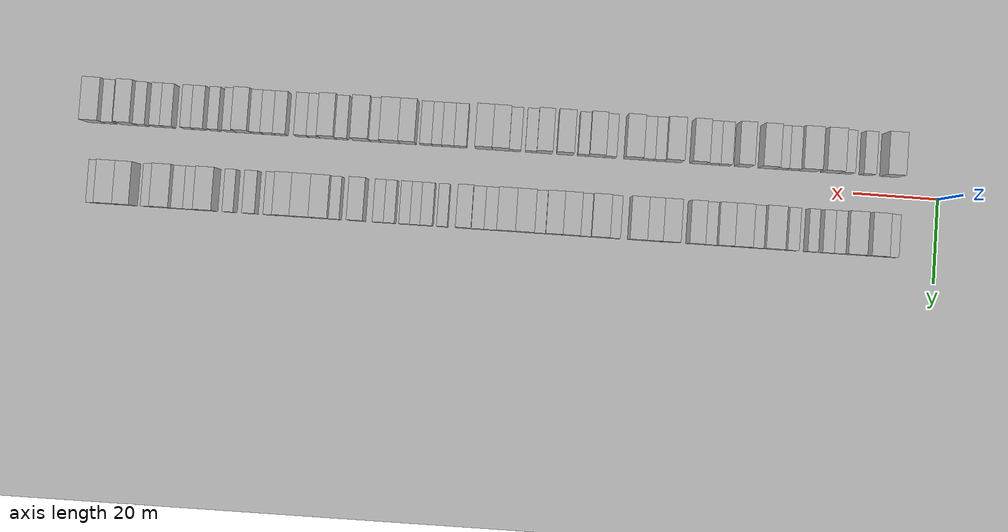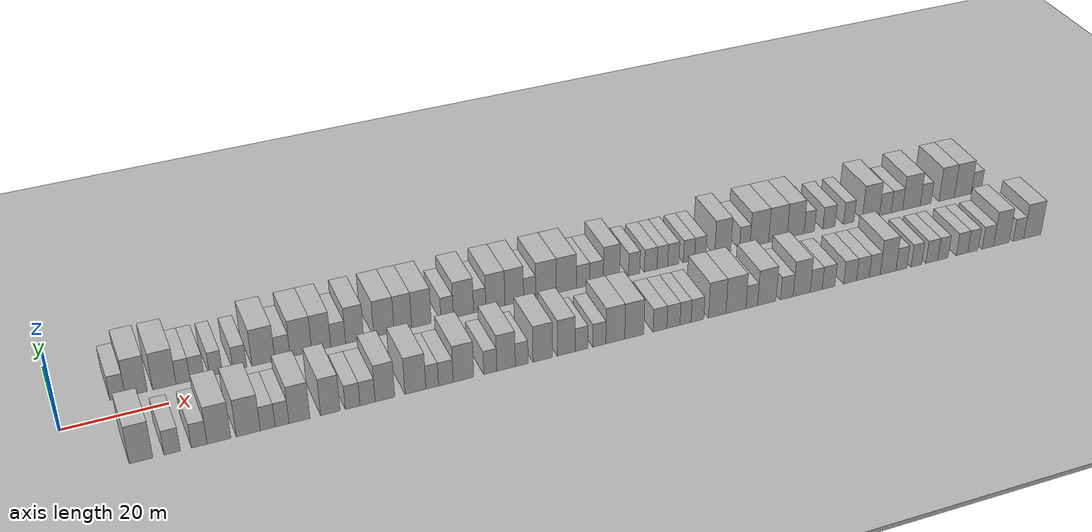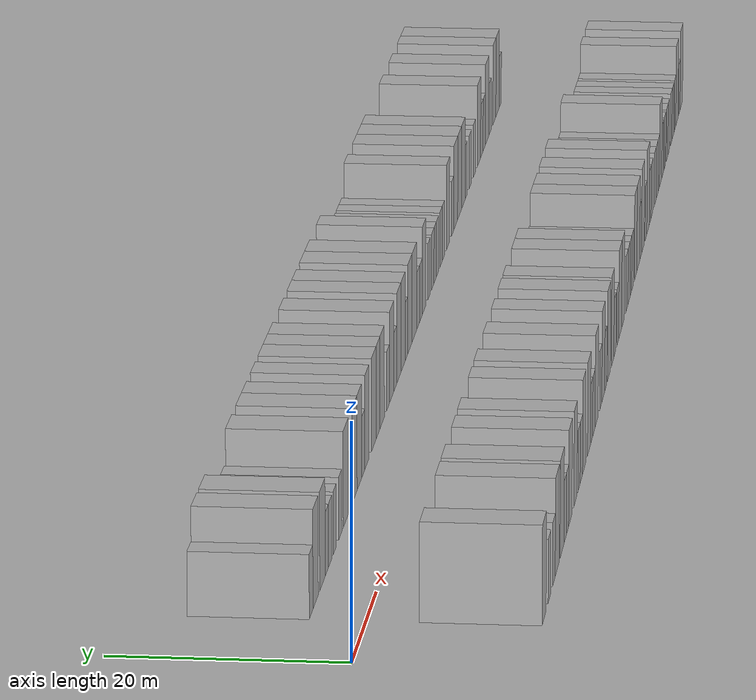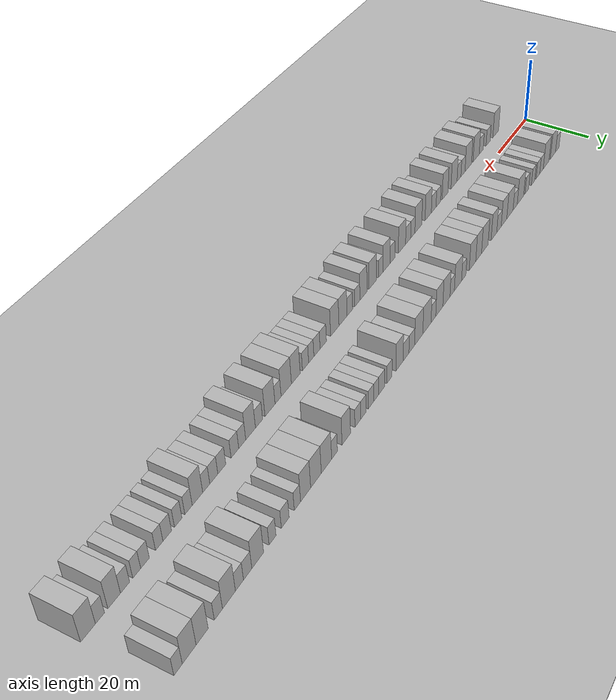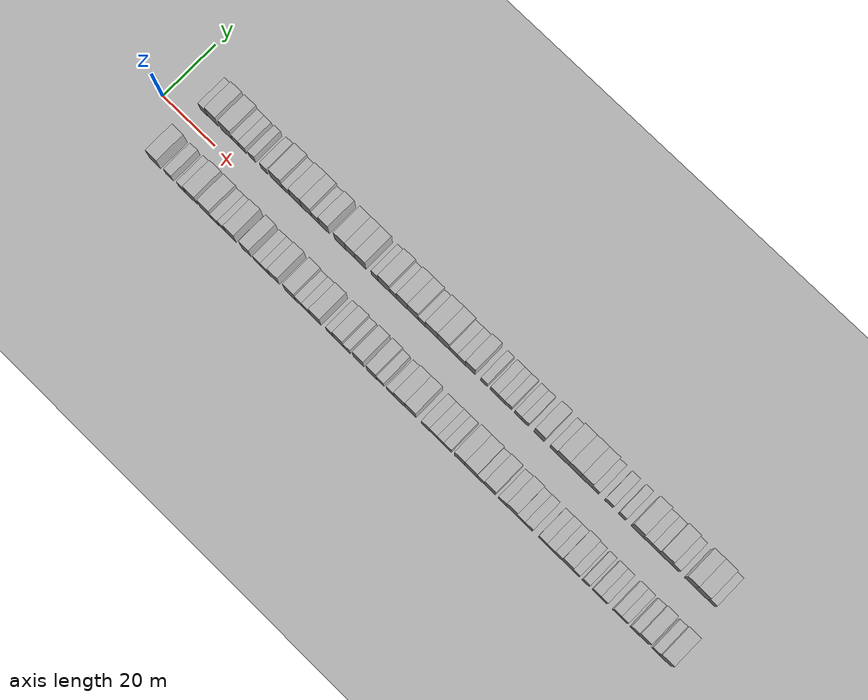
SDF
<?xml version="1.0" encoding="utf-8"?>

<sdf version="1.6">

   <world name="default">

      <gui fullscreen="0">

         <camera name="user_camera">

            <pose>-15 0 4.57585 0 0 0</pose>

            <view_controller>orbit</view_controller>

         </camera>

      </gui>

      <scene>

         <sky>

           <clouds>

             <speed>12</speed>

           </clouds>

         </sky>

         <ambient>0.4 0.4 0.4 1</ambient>

         <background>0.7 0.7 0.7 1</background>

         <shadows>1</shadows>

      </scene>

      <gravity>0 0 -9.8066</gravity>

      <magnetic_field>6e-06 2.3e-05 -4.2e-05</magnetic_field>

      <physics default="0" name="default_physics" type="ode">

         <ode>

            <solver>

               <type>quick</type>

               <iters>10</iters>

               <sor>1.0</sor>

               <use_dynamic_moi_rescaling>0</use_dynamic_moi_rescaling>

            </solver>

            <constraints>

               <cfm>0</cfm>

               <erp>0.2</erp>

               <contact_max_correcting_vel>100</contact_max_correcting_vel>

               <contact_surface_layer>0.001</contact_surface_layer>

            </constraints>

         </ode>

         <max_step_size>0.004</max_step_size>

         <real_time_factor>1</real_time_factor>

         <real_time_update_rate>250</real_time_update_rate>

      </physics>

      <light name="sun" type="directional">

         <cast_shadows>1</cast_shadows>

         <pose>0 0 10 0 0 0</pose>

         <diffuse>0.8 0.8 0.8 1</diffuse>

         <specular>0.2 0.2 0.2 1</specular>

         <attenuation>

            <range>1000</range>

            <constant>0.9</constant>

            <linear>0.01</linear>

            <quadratic>0.001</quadratic>

         </attenuation>

         <direction>-0.5 0.1 -0.9</direction>

      </light>

      <include>

         <name>ground_plane_1</name>

         <uri>model://HANNAS_ground_plane</uri>

         <pose>0 0 0  0 0 0</pose>

      </include>

      <include>

         <name>ground_plane_2</name>

         <uri>model://HANNAS_ground_plane</uri>

         <pose>100 0 0  0 0 0</pose>

      </include>

      <model name="building_1">

         <static>1</static>

         <pose frame="">11.4239 9.5000 0 0.000000 0.000000 1.570796</pose>

         <link name="link">

            <pose frame="">0 0 3.00 0 0 0</pose>

            <collision name="collision">

               <geometry>

                  <box>

                     <size>10.0000 2.8477 6.0000</size>

                  </box>

               </geometry>

               <max_contacts>10</max_contacts>

               <surface>

                  <contact>

                     <ode/>

                  </contact>

                  <bounce/>

                  <friction>

                     <torsional>

                        <ode/>

                     </torsional>

                     <ode/>

                  </friction>

               </surface>

            </collision>

            <visual name="visual">

               <cast_shadows>0</cast_shadows>

               <geometry>

                  <box>

                     <size>10.0000 2.8477 6.0000</size>

                  </box>

               </geometry>

               <material>

                  <script>

                     <uri>model://HANNAS_wall/materials/scripts</uri>

                     <uri>model://HANNAS_wall/materials/textures</uri>

                     <name>vrc/HANNAS_wall</name>

                  </script>

               </material>

            </visual>

            <self_collide>0</self_collide>

            <enable_wind>0</enable_wind>

            <kinematic>0</kinematic>

         </link>

      </model>

      <model name="building_2">

         <static>1</static>

         <pose frame="">14.9060 9.5000 0 0.000000 0.000000 1.570796</pose>

         <link name="link">

            <pose frame="">0 0 4.50 0 0 0</pose>

            <collision name="collision">

               <geometry>

                  <box>

                     <size>10.0000 4.1167 9.0000</size>

                  </box>

               </geometry>

               <max_contacts>10</max_contacts>

               <surface>

                  <contact>

                     <ode/>

                  </contact>

                  <bounce/>

                  <friction>

                     <torsional>

                        <ode/>

                     </torsional>

                     <ode/>

                  </friction>

               </surface>

            </collision>

            <visual name="visual">

               <cast_shadows>0</cast_shadows>

               <geometry>

                  <box>

                     <size>10.0000 4.1167 9.0000</size>

                  </box>

               </geometry>

               <material>

                  <script>

                     <uri>model://HANNAS_wall/materials/scripts</uri>

                     <uri>model://HANNAS_wall/materials/textures</uri>

                     <name>vrc/HANNAS_wall</name>

                  </script>

               </material>

            </visual>

            <self_collide>0</self_collide>

            <enable_wind>0</enable_wind>

            <kinematic>0</kinematic>

         </link>

      </model>

      <model name="building_3">

         <static>1</static>

         <pose frame="">20.1691 9.5000 0 0.000000 0.000000 1.570796</pose>

         <link name="link">

            <pose frame="">0 0 4.50 0 0 0</pose>

            <collision name="collision">

               <geometry>

                  <box>

                     <size>10.0000 4.4095 9.0000</size>

                  </box>

               </geometry>

               <max_contacts>10</max_contacts>

               <surface>

                  <contact>

                     <ode/>

                  </contact>

                  <bounce/>

                  <friction>

                     <torsional>

                        <ode/>

                     </torsional>

                     <ode/>

                  </friction>

               </surface>

            </collision>

            <visual name="visual">

               <cast_shadows>0</cast_shadows>

               <geometry>

                  <box>

                     <size>10.0000 4.4095 9.0000</size>

                  </box>

               </geometry>

               <material>

                  <script>

                     <uri>model://HANNAS_wall/materials/scripts</uri>

                     <uri>model://HANNAS_wall/materials/textures</uri>

                     <name>vrc/HANNAS_wall</name>

                  </script>

               </material>

            </visual>

            <self_collide>0</self_collide>

            <enable_wind>0</enable_wind>

            <kinematic>0</kinematic>

         </link>

      </model>

      <model name="building_4">

         <static>1</static>

         <pose frame="">23.7036 9.5000 0 0.000000 0.000000 1.570796</pose>

         <link name="link">

            <pose frame="">0 0 3.00 0 0 0</pose>

            <collision name="collision">

               <geometry>

                  <box>

                     <size>10.0000 2.6595 6.0000</size>

                  </box>

               </geometry>

               <max_contacts>10</max_contacts>

               <surface>

                  <contact>

                     <ode/>

                  </contact>

                  <bounce/>

                  <friction>

                     <torsional>

                        <ode/>

                     </torsional>

                     <ode/>

                  </friction>

               </surface>

            </collision>

            <visual name="visual">

               <cast_shadows>0</cast_shadows>

               <geometry>

                  <box>

                     <size>10.0000 2.6595 6.0000</size>

                  </box>

               </geometry>

               <material>

                  <script>

                     <uri>model://HANNAS_wall/materials/scripts</uri>

                     <uri>model://HANNAS_wall/materials/textures</uri>

                     <name>vrc/HANNAS_wall</name>

                  </script>

               </material>

            </visual>

            <self_collide>0</self_collide>

            <enable_wind>0</enable_wind>

            <kinematic>0</kinematic>

         </link>

      </model>

      <model name="building_5">

         <static>1</static>

         <pose frame="">26.3857 9.5000 0 0.000000 0.000000 1.570796</pose>

         <link name="link">

            <pose frame="">0 0 3.00 0 0 0</pose>

            <collision name="collision">

               <geometry>

                  <box>

                     <size>10.0000 2.7047 6.0000</size>

                  </box>

               </geometry>

               <max_contacts>10</max_contacts>

               <surface>

                  <contact>

                     <ode/>

                  </contact>

                  <bounce/>

                  <friction>

                     <torsional>

                        <ode/>

                     </torsional>

                     <ode/>

                  </friction>

               </surface>

            </collision>

            <visual name="visual">

               <cast_shadows>0</cast_shadows>

               <geometry>

                  <box>

                     <size>10.0000 2.7047 6.0000</size>

                  </box>

               </geometry>

               <material>

                  <script>

                     <uri>model://HANNAS_wall/materials/scripts</uri>

                     <uri>model://HANNAS_wall/materials/textures</uri>

                     <name>vrc/HANNAS_wall</name>

                  </script>

               </material>

            </visual>

            <self_collide>0</self_collide>

            <enable_wind>0</enable_wind>

            <kinematic>0</kinematic>

         </link>

      </model>

      <model name="building_6">

         <static>1</static>

         <pose frame="">29.9758 9.5000 0 0.000000 0.000000 1.570796</pose>

         <link name="link">

            <pose frame="">0 0 3.00 0 0 0</pose>

            <collision name="collision">

               <geometry>

                  <box>

                     <size>10.0000 2.4755 6.0000</size>

                  </box>

               </geometry>

               <max_contacts>10</max_contacts>

               <surface>

                  <contact>

                     <ode/>

                  </contact>

                  <bounce/>

                  <friction>

                     <torsional>

                        <ode/>

                     </torsional>

                     <ode/>

                  </friction>

               </surface>

            </collision>

            <visual name="visual">

               <cast_shadows>0</cast_shadows>

               <geometry>

                  <box>

                     <size>10.0000 2.4755 6.0000</size>

                  </box>

               </geometry>

               <material>

                  <script>

                     <uri>model://HANNAS_wall/materials/scripts</uri>

                     <uri>model://HANNAS_wall/materials/textures</uri>

                     <name>vrc/HANNAS_wall</name>

                  </script>

               </material>

            </visual>

            <self_collide>0</self_collide>

            <enable_wind>0</enable_wind>

            <kinematic>0</kinematic>

         </link>

      </model>

      <model name="building_7">

         <static>1</static>

         <pose frame="">34.5574 9.5000 0 0.000000 0.000000 1.570796</pose>

         <link name="link">

            <pose frame="">0 0 3.00 0 0 0</pose>

            <collision name="collision">

               <geometry>

                  <box>

                     <size>10.0000 2.6878 6.0000</size>

                  </box>

               </geometry>

               <max_contacts>10</max_contacts>

               <surface>

                  <contact>

                     <ode/>

                  </contact>

                  <bounce/>

                  <friction>

                     <torsional>

                        <ode/>

                     </torsional>

                     <ode/>

                  </friction>

               </surface>

            </collision>

            <visual name="visual">

               <cast_shadows>0</cast_shadows>

               <geometry>

                  <box>

                     <size>10.0000 2.6878 6.0000</size>

                  </box>

               </geometry>

               <material>

                  <script>

                     <uri>model://HANNAS_wall/materials/scripts</uri>

                     <uri>model://HANNAS_wall/materials/textures</uri>

                     <name>vrc/HANNAS_wall</name>

                  </script>

               </material>

            </visual>

            <self_collide>0</self_collide>

            <enable_wind>0</enable_wind>

            <kinematic>0</kinematic>

         </link>

      </model>

      <model name="building_8">

         <static>1</static>

         <pose frame="">39.1502 9.5000 0 0.000000 0.000000 1.570796</pose>

         <link name="link">

            <pose frame="">0 0 4.50 0 0 0</pose>

            <collision name="collision">

               <geometry>

                  <box>

                     <size>10.0000 4.4978 9.0000</size>

                  </box>

               </geometry>

               <max_contacts>10</max_contacts>

               <surface>

                  <contact>

                     <ode/>

                  </contact>

                  <bounce/>

                  <friction>

                     <torsional>

                        <ode/>

                     </torsional>

                     <ode/>

                  </friction>

               </surface>

            </collision>

            <visual name="visual">

               <cast_shadows>0</cast_shadows>

               <geometry>

                  <box>

                     <size>10.0000 4.4978 9.0000</size>

                  </box>

               </geometry>

               <material>

                  <script>

                     <uri>model://HANNAS_wall/materials/scripts</uri>

                     <uri>model://HANNAS_wall/materials/textures</uri>

                     <name>vrc/HANNAS_wall</name>

                  </script>

               </material>

            </visual>

            <self_collide>0</self_collide>

            <enable_wind>0</enable_wind>

            <kinematic>0</kinematic>

         </link>

      </model>

      <model name="building_9">

         <static>1</static>

         <pose frame="">42.8805 9.5000 0 0.000000 0.000000 1.570796</pose>

         <link name="link">

            <pose frame="">0 0 3.00 0 0 0</pose>

            <collision name="collision">

               <geometry>

                  <box>

                     <size>10.0000 2.9629 6.0000</size>

                  </box>

               </geometry>

               <max_contacts>10</max_contacts>

               <surface>

                  <contact>

                     <ode/>

                  </contact>

                  <bounce/>

                  <friction>

                     <torsional>

                        <ode/>

                     </torsional>

                     <ode/>

                  </friction>

               </surface>

            </collision>

            <visual name="visual">

               <cast_shadows>0</cast_shadows>

               <geometry>

                  <box>

                     <size>10.0000 2.9629 6.0000</size>

                  </box>

               </geometry>

               <material>

                  <script>

                     <uri>model://HANNAS_wall/materials/scripts</uri>

                     <uri>model://HANNAS_wall/materials/textures</uri>

                     <name>vrc/HANNAS_wall</name>

                  </script>

               </material>

            </visual>

            <self_collide>0</self_collide>

            <enable_wind>0</enable_wind>

            <kinematic>0</kinematic>

         </link>

      </model>

      <model name="building_10">

         <static>1</static>

         <pose frame="">46.5020 9.5000 0 0.000000 0.000000 1.570796</pose>

         <link name="link">

            <pose frame="">0 0 4.50 0 0 0</pose>

            <collision name="collision">

               <geometry>

                  <box>

                     <size>10.0000 4.2799 9.0000</size>

                  </box>

               </geometry>

               <max_contacts>10</max_contacts>

               <surface>

                  <contact>

                     <ode/>

                  </contact>

                  <bounce/>

                  <friction>

                     <torsional>

                        <ode/>

                     </torsional>

                     <ode/>

                  </friction>

               </surface>

            </collision>

            <visual name="visual">

               <cast_shadows>0</cast_shadows>

               <geometry>

                  <box>

                     <size>10.0000 4.2799 9.0000</size>

                  </box>

               </geometry>

               <material>

                  <script>

                     <uri>model://HANNAS_wall/materials/scripts</uri>

                     <uri>model://HANNAS_wall/materials/textures</uri>

                     <name>vrc/HANNAS_wall</name>

                  </script>

               </material>

            </visual>

            <self_collide>0</self_collide>

            <enable_wind>0</enable_wind>

            <kinematic>0</kinematic>

         </link>

      </model>

      <model name="building_11">

         <static>1</static>

         <pose frame="">50.5409 9.5000 0 0.000000 0.000000 1.570796</pose>

         <link name="link">

            <pose frame="">0 0 4.50 0 0 0</pose>

            <collision name="collision">

               <geometry>

                  <box>

                     <size>10.0000 3.7978 9.0000</size>

                  </box>

               </geometry>

               <max_contacts>10</max_contacts>

               <surface>

                  <contact>

                     <ode/>

                  </contact>

                  <bounce/>

                  <friction>

                     <torsional>

                        <ode/>

                     </torsional>

                     <ode/>

                  </friction>

               </surface>

            </collision>

            <visual name="visual">

               <cast_shadows>0</cast_shadows>

               <geometry>

                  <box>

                     <size>10.0000 3.7978 9.0000</size>

                  </box>

               </geometry>

               <material>

                  <script>

                     <uri>model://HANNAS_wall/materials/scripts</uri>

                     <uri>model://HANNAS_wall/materials/textures</uri>

                     <name>vrc/HANNAS_wall</name>

                  </script>

               </material>

            </visual>

            <self_collide>0</self_collide>

            <enable_wind>0</enable_wind>

            <kinematic>0</kinematic>

         </link>

      </model>

      <model name="building_12">

         <static>1</static>

         <pose frame="">53.9195 9.5000 0 0.000000 0.000000 1.570796</pose>

         <link name="link">

            <pose frame="">0 0 3.00 0 0 0</pose>

            <collision name="collision">

               <geometry>

                  <box>

                     <size>10.0000 2.9594 6.0000</size>

                  </box>

               </geometry>

               <max_contacts>10</max_contacts>

               <surface>

                  <contact>

                     <ode/>

                  </contact>

                  <bounce/>

                  <friction>

                     <torsional>

                        <ode/>

                     </torsional>

                     <ode/>

                  </friction>

               </surface>

            </collision>

            <visual name="visual">

               <cast_shadows>0</cast_shadows>

               <geometry>

                  <box>

                     <size>10.0000 2.9594 6.0000</size>

                  </box>

               </geometry>

               <material>

                  <script>

                     <uri>model://HANNAS_wall/materials/scripts</uri>

                     <uri>model://HANNAS_wall/materials/textures</uri>

                     <name>vrc/HANNAS_wall</name>

                  </script>

               </material>

            </visual>

            <self_collide>0</self_collide>

            <enable_wind>0</enable_wind>

            <kinematic>0</kinematic>

         </link>

      </model>

      <model name="building_13">

         <static>1</static>

         <pose frame="">57.2381 9.5000 0 0.000000 0.000000 1.570796</pose>

         <link name="link">

            <pose frame="">0 0 4.50 0 0 0</pose>

            <collision name="collision">

               <geometry>

                  <box>

                     <size>10.0000 3.6779 9.0000</size>

                  </box>

               </geometry>

               <max_contacts>10</max_contacts>

               <surface>

                  <contact>

                     <ode/>

                  </contact>

                  <bounce/>

                  <friction>

                     <torsional>

                        <ode/>

                     </torsional>

                     <ode/>

                  </friction>

               </surface>

            </collision>

            <visual name="visual">

               <cast_shadows>0</cast_shadows>

               <geometry>

                  <box>

                     <size>10.0000 3.6779 9.0000</size>

                  </box>

               </geometry>

               <material>

                  <script>

                     <uri>model://HANNAS_wall/materials/scripts</uri>

                     <uri>model://HANNAS_wall/materials/textures</uri>

                     <name>vrc/HANNAS_wall</name>

                  </script>

               </material>

            </visual>

            <self_collide>0</self_collide>

            <enable_wind>0</enable_wind>

            <kinematic>0</kinematic>

         </link>

      </model>

      <model name="building_14">

         <static>1</static>

         <pose frame="">63.1464 9.5000 0 0.000000 0.000000 1.570796</pose>

         <link name="link">

            <pose frame="">0 0 4.50 0 0 0</pose>

            <collision name="collision">

               <geometry>

                  <box>

                     <size>10.0000 4.1388 9.0000</size>

                  </box>

               </geometry>

               <max_contacts>10</max_contacts>

               <surface>

                  <contact>

                     <ode/>

                  </contact>

                  <bounce/>

                  <friction>

                     <torsional>

                        <ode/>

                     </torsional>

                     <ode/>

                  </friction>

               </surface>

            </collision>

            <visual name="visual">

               <cast_shadows>0</cast_shadows>

               <geometry>

                  <box>

                     <size>10.0000 4.1388 9.0000</size>

                  </box>

               </geometry>

               <material>

                  <script>

                     <uri>model://HANNAS_wall/materials/scripts</uri>

                     <uri>model://HANNAS_wall/materials/textures</uri>

                     <name>vrc/HANNAS_wall</name>

                  </script>

               </material>

            </visual>

            <self_collide>0</self_collide>

            <enable_wind>0</enable_wind>

            <kinematic>0</kinematic>

         </link>

      </model>

      <model name="building_15">

         <static>1</static>

         <pose frame="">67.0184 9.5000 0 0.000000 0.000000 1.570796</pose>

         <link name="link">

            <pose frame="">0 0 4.50 0 0 0</pose>

            <collision name="collision">

               <geometry>

                  <box>

                     <size>10.0000 3.6050 9.0000</size>

                  </box>

               </geometry>

               <max_contacts>10</max_contacts>

               <surface>

                  <contact>

                     <ode/>

                  </contact>

                  <bounce/>

                  <friction>

                     <torsional>

                        <ode/>

                     </torsional>

                     <ode/>

                  </friction>

               </surface>

            </collision>

            <visual name="visual">

               <cast_shadows>0</cast_shadows>

               <geometry>

                  <box>

                     <size>10.0000 3.6050 9.0000</size>

                  </box>

               </geometry>

               <material>

                  <script>

                     <uri>model://HANNAS_wall/materials/scripts</uri>

                     <uri>model://HANNAS_wall/materials/textures</uri>

                     <name>vrc/HANNAS_wall</name>

                  </script>

               </material>

            </visual>

            <self_collide>0</self_collide>

            <enable_wind>0</enable_wind>

            <kinematic>0</kinematic>

         </link>

      </model>

      <model name="building_16">

         <static>1</static>

         <pose frame="">70.8393 9.5000 0 0.000000 0.000000 1.570796</pose>

         <link name="link">

            <pose frame="">0 0 4.50 0 0 0</pose>

            <collision name="collision">

               <geometry>

                  <box>

                     <size>10.0000 4.0368 9.0000</size>

                  </box>

               </geometry>

               <max_contacts>10</max_contacts>

               <surface>

                  <contact>

                     <ode/>

                  </contact>

                  <bounce/>

                  <friction>

                     <torsional>

                        <ode/>

                     </torsional>

                     <ode/>

                  </friction>

               </surface>

            </collision>

            <visual name="visual">

               <cast_shadows>0</cast_shadows>

               <geometry>

                  <box>

                     <size>10.0000 4.0368 9.0000</size>

                  </box>

               </geometry>

               <material>

                  <script>

                     <uri>model://HANNAS_wall/materials/scripts</uri>

                     <uri>model://HANNAS_wall/materials/textures</uri>

                     <name>vrc/HANNAS_wall</name>

                  </script>

               </material>

            </visual>

            <self_collide>0</self_collide>

            <enable_wind>0</enable_wind>

            <kinematic>0</kinematic>

         </link>

      </model>

      <model name="building_17">

         <static>1</static>

         <pose frame="">76.1547 9.5000 0 0.000000 0.000000 1.570796</pose>

         <link name="link">

            <pose frame="">0 0 3.00 0 0 0</pose>

            <collision name="collision">

               <geometry>

                  <box>

                     <size>10.0000 2.5940 6.0000</size>

                  </box>

               </geometry>

               <max_contacts>10</max_contacts>

               <surface>

                  <contact>

                     <ode/>

                  </contact>

                  <bounce/>

                  <friction>

                     <torsional>

                        <ode/>

                     </torsional>

                     <ode/>

                  </friction>

               </surface>

            </collision>

            <visual name="visual">

               <cast_shadows>0</cast_shadows>

               <geometry>

                  <box>

                     <size>10.0000 2.5940 6.0000</size>

                  </box>

               </geometry>

               <material>

                  <script>

                     <uri>model://HANNAS_wall/materials/scripts</uri>

                     <uri>model://HANNAS_wall/materials/textures</uri>

                     <name>vrc/HANNAS_wall</name>

                  </script>

               </material>

            </visual>

            <self_collide>0</self_collide>

            <enable_wind>0</enable_wind>

            <kinematic>0</kinematic>

         </link>

      </model>

      <model name="building_18">

         <static>1</static>

         <pose frame="">79.5882 9.5000 0 0.000000 0.000000 1.570796</pose>

         <link name="link">

            <pose frame="">0 0 4.50 0 0 0</pose>

            <collision name="collision">

               <geometry>

                  <box>

                     <size>10.0000 4.2730 9.0000</size>

                  </box>

               </geometry>

               <max_contacts>10</max_contacts>

               <surface>

                  <contact>

                     <ode/>

                  </contact>

                  <bounce/>

                  <friction>

                     <torsional>

                        <ode/>

                     </torsional>

                     <ode/>

                  </friction>

               </surface>

            </collision>

            <visual name="visual">

               <cast_shadows>0</cast_shadows>

               <geometry>

                  <box>

                     <size>10.0000 4.2730 9.0000</size>

                  </box>

               </geometry>

               <material>

                  <script>

                     <uri>model://HANNAS_wall/materials/scripts</uri>

                     <uri>model://HANNAS_wall/materials/textures</uri>

                     <name>vrc/HANNAS_wall</name>

                  </script>

               </material>

            </visual>

            <self_collide>0</self_collide>

            <enable_wind>0</enable_wind>

            <kinematic>0</kinematic>

         </link>

      </model>

      <model name="building_19">

         <static>1</static>

         <pose frame="">83.0077 9.5000 0 0.000000 0.000000 1.570796</pose>

         <link name="link">

            <pose frame="">0 0 3.00 0 0 0</pose>

            <collision name="collision">

               <geometry>

                  <box>

                     <size>10.0000 2.5660 6.0000</size>

                  </box>

               </geometry>

               <max_contacts>10</max_contacts>

               <surface>

                  <contact>

                     <ode/>

                  </contact>

                  <bounce/>

                  <friction>

                     <torsional>

                        <ode/>

                     </torsional>

                     <ode/>

                  </friction>

               </surface>

            </collision>

            <visual name="visual">

               <cast_shadows>0</cast_shadows>

               <geometry>

                  <box>

                     <size>10.0000 2.5660 6.0000</size>

                  </box>

               </geometry>

               <material>

                  <script>

                     <uri>model://HANNAS_wall/materials/scripts</uri>

                     <uri>model://HANNAS_wall/materials/textures</uri>

                     <name>vrc/HANNAS_wall</name>

                  </script>

               </material>

            </visual>

            <self_collide>0</self_collide>

            <enable_wind>0</enable_wind>

            <kinematic>0</kinematic>

         </link>

      </model>

      <model name="building_20">

         <static>1</static>

         <pose frame="">86.3215 9.5000 0 0.000000 0.000000 1.570796</pose>

         <link name="link">

            <pose frame="">0 0 4.50 0 0 0</pose>

            <collision name="collision">

               <geometry>

                  <box>

                     <size>10.0000 4.0616 9.0000</size>

                  </box>

               </geometry>

               <max_contacts>10</max_contacts>

               <surface>

                  <contact>

                     <ode/>

                  </contact>

                  <bounce/>

                  <friction>

                     <torsional>

                        <ode/>

                     </torsional>

                     <ode/>

                  </friction>

               </surface>

            </collision>

            <visual name="visual">

               <cast_shadows>0</cast_shadows>

               <geometry>

                  <box>

                     <size>10.0000 4.0616 9.0000</size>

                  </box>

               </geometry>

               <material>

                  <script>

                     <uri>model://HANNAS_wall/materials/scripts</uri>

                     <uri>model://HANNAS_wall/materials/textures</uri>

                     <name>vrc/HANNAS_wall</name>

                  </script>

               </material>

            </visual>

            <self_collide>0</self_collide>

            <enable_wind>0</enable_wind>

            <kinematic>0</kinematic>

         </link>

      </model>

      <model name="building_21">

         <static>1</static>

         <pose frame="">90.3455 9.5000 0 0.000000 0.000000 1.570796</pose>

         <link name="link">

            <pose frame="">0 0 4.50 0 0 0</pose>

            <collision name="collision">

               <geometry>

                  <box>

                     <size>10.0000 3.9864 9.0000</size>

                  </box>

               </geometry>

               <max_contacts>10</max_contacts>

               <surface>

                  <contact>

                     <ode/>

                  </contact>

                  <bounce/>

                  <friction>

                     <torsional>

                        <ode/>

                     </torsional>

                     <ode/>

                  </friction>

               </surface>

            </collision>

            <visual name="visual">

               <cast_shadows>0</cast_shadows>

               <geometry>

                  <box>

                     <size>10.0000 3.9864 9.0000</size>

                  </box>

               </geometry>

               <material>

                  <script>

                     <uri>model://HANNAS_wall/materials/scripts</uri>

                     <uri>model://HANNAS_wall/materials/textures</uri>

                     <name>vrc/HANNAS_wall</name>

                  </script>

               </material>

            </visual>

            <self_collide>0</self_collide>

            <enable_wind>0</enable_wind>

            <kinematic>0</kinematic>

         </link>

      </model>

      <model name="building_22">

         <static>1</static>

         <pose frame="">93.6370 9.5000 0 0.000000 0.000000 1.570796</pose>

         <link name="link">

            <pose frame="">0 0 3.00 0 0 0</pose>

            <collision name="collision">

               <geometry>

                  <box>

                     <size>10.0000 2.5968 6.0000</size>

                  </box>

               </geometry>

               <max_contacts>10</max_contacts>

               <surface>

                  <contact>

                     <ode/>

                  </contact>

                  <bounce/>

                  <friction>

                     <torsional>

                        <ode/>

                     </torsional>

                     <ode/>

                  </friction>

               </surface>

            </collision>

            <visual name="visual">

               <cast_shadows>0</cast_shadows>

               <geometry>

                  <box>

                     <size>10.0000 2.5968 6.0000</size>

                  </box>

               </geometry>

               <material>

                  <script>

                     <uri>model://HANNAS_wall/materials/scripts</uri>

                     <uri>model://HANNAS_wall/materials/textures</uri>

                     <name>vrc/HANNAS_wall</name>

                  </script>

               </material>

            </visual>

            <self_collide>0</self_collide>

            <enable_wind>0</enable_wind>

            <kinematic>0</kinematic>

         </link>

      </model>

      <model name="building_23">

         <static>1</static>

         <pose frame="">97.1572 9.5000 0 0.000000 0.000000 1.570796</pose>

         <link name="link">

            <pose frame="">0 0 4.50 0 0 0</pose>

            <collision name="collision">

               <geometry>

                  <box>

                     <size>10.0000 4.4437 9.0000</size>

                  </box>

               </geometry>

               <max_contacts>10</max_contacts>

               <surface>

                  <contact>

                     <ode/>

                  </contact>

                  <bounce/>

                  <friction>

                     <torsional>

                        <ode/>

                     </torsional>

                     <ode/>

                  </friction>

               </surface>

            </collision>

            <visual name="visual">

               <cast_shadows>0</cast_shadows>

               <geometry>

                  <box>

                     <size>10.0000 4.4437 9.0000</size>

                  </box>

               </geometry>

               <material>

                  <script>

                     <uri>model://HANNAS_wall/materials/scripts</uri>

                     <uri>model://HANNAS_wall/materials/textures</uri>

                     <name>vrc/HANNAS_wall</name>

                  </script>

               </material>

            </visual>

            <self_collide>0</self_collide>

            <enable_wind>0</enable_wind>

            <kinematic>0</kinematic>

         </link>

      </model>

      <model name="building_24">

         <static>1</static>

         <pose frame="">101.5641 9.5000 0 0.000000 0.000000 1.570796</pose>

         <link name="link">

            <pose frame="">0 0 4.50 0 0 0</pose>

            <collision name="collision">

               <geometry>

                  <box>

                     <size>10.0000 4.3701 9.0000</size>

                  </box>

               </geometry>

               <max_contacts>10</max_contacts>

               <surface>

                  <contact>

                     <ode/>

                  </contact>

                  <bounce/>

                  <friction>

                     <torsional>

                        <ode/>

                     </torsional>

                     <ode/>

                  </friction>

               </surface>

            </collision>

            <visual name="visual">

               <cast_shadows>0</cast_shadows>

               <geometry>

                  <box>

                     <size>10.0000 4.3701 9.0000</size>

                  </box>

               </geometry>

               <material>

                  <script>

                     <uri>model://HANNAS_wall/materials/scripts</uri>

                     <uri>model://HANNAS_wall/materials/textures</uri>

                     <name>vrc/HANNAS_wall</name>

                  </script>

               </material>

            </visual>

            <self_collide>0</self_collide>

            <enable_wind>0</enable_wind>

            <kinematic>0</kinematic>

         </link>

      </model>

      <model name="building_25">

         <static>1</static>

         <pose frame="">105.2308 9.5000 0 0.000000 0.000000 1.570796</pose>

         <link name="link">

            <pose frame="">0 0 3.00 0 0 0</pose>

            <collision name="collision">

               <geometry>

                  <box>

                     <size>10.0000 2.9633 6.0000</size>

                  </box>

               </geometry>

               <max_contacts>10</max_contacts>

               <surface>

                  <contact>

                     <ode/>

                  </contact>

                  <bounce/>

                  <friction>

                     <torsional>

                        <ode/>

                     </torsional>

                     <ode/>

                  </friction>

               </surface>

            </collision>

            <visual name="visual">

               <cast_shadows>0</cast_shadows>

               <geometry>

                  <box>

                     <size>10.0000 2.9633 6.0000</size>

                  </box>

               </geometry>

               <material>

                  <script>

                     <uri>model://HANNAS_wall/materials/scripts</uri>

                     <uri>model://HANNAS_wall/materials/textures</uri>

                     <name>vrc/HANNAS_wall</name>

                  </script>

               </material>

            </visual>

            <self_collide>0</self_collide>

            <enable_wind>0</enable_wind>

            <kinematic>0</kinematic>

         </link>

      </model>

      <model name="building_26">

         <static>1</static>

         <pose frame="">108.1877 9.5000 0 0.000000 0.000000 1.570796</pose>

         <link name="link">

            <pose frame="">0 0 3.00 0 0 0</pose>

            <collision name="collision">

               <geometry>

                  <box>

                     <size>10.0000 2.9506 6.0000</size>

                  </box>

               </geometry>

               <max_contacts>10</max_contacts>

               <surface>

                  <contact>

                     <ode/>

                  </contact>

                  <bounce/>

                  <friction>

                     <torsional>

                        <ode/>

                     </torsional>

                     <ode/>

                  </friction>

               </surface>

            </collision>

            <visual name="visual">

               <cast_shadows>0</cast_shadows>

               <geometry>

                  <box>

                     <size>10.0000 2.9506 6.0000</size>

                  </box>

               </geometry>

               <material>

                  <script>

                     <uri>model://HANNAS_wall/materials/scripts</uri>

                     <uri>model://HANNAS_wall/materials/textures</uri>

                     <name>vrc/HANNAS_wall</name>

                  </script>

               </material>

            </visual>

            <self_collide>0</self_collide>

            <enable_wind>0</enable_wind>

            <kinematic>0</kinematic>

         </link>

      </model>

      <model name="building_27">

         <static>1</static>

         <pose frame="">111.4786 9.5000 0 0.000000 0.000000 1.570796</pose>

         <link name="link">

            <pose frame="">0 0 4.50 0 0 0</pose>

            <collision name="collision">

               <geometry>

                  <box>

                     <size>10.0000 3.6313 9.0000</size>

                  </box>

               </geometry>

               <max_contacts>10</max_contacts>

               <surface>

                  <contact>

                     <ode/>

                  </contact>

                  <bounce/>

                  <friction>

                     <torsional>

                        <ode/>

                     </torsional>

                     <ode/>

                  </friction>

               </surface>

            </collision>

            <visual name="visual">

               <cast_shadows>0</cast_shadows>

               <geometry>

                  <box>

                     <size>10.0000 3.6313 9.0000</size>

                  </box>

               </geometry>

               <material>

                  <script>

                     <uri>model://HANNAS_wall/materials/scripts</uri>

                     <uri>model://HANNAS_wall/materials/textures</uri>

                     <name>vrc/HANNAS_wall</name>

                  </script>

               </material>

            </visual>

            <self_collide>0</self_collide>

            <enable_wind>0</enable_wind>

            <kinematic>0</kinematic>

         </link>

      </model>

      <model name="building_28">

         <static>1</static>

         <pose frame="">116.5506 9.5000 0 0.000000 0.000000 1.570796</pose>

         <link name="link">

            <pose frame="">0 0 3.00 0 0 0</pose>

            <collision name="collision">

               <geometry>

                  <box>

                     <size>10.0000 2.5127 6.0000</size>

                  </box>

               </geometry>

               <max_contacts>10</max_contacts>

               <surface>

                  <contact>

                     <ode/>

                  </contact>

                  <bounce/>

                  <friction>

                     <torsional>

                        <ode/>

                     </torsional>

                     <ode/>

                  </friction>

               </surface>

            </collision>

            <visual name="visual">

               <cast_shadows>0</cast_shadows>

               <geometry>

                  <box>

                     <size>10.0000 2.5127 6.0000</size>

                  </box>

               </geometry>

               <material>

                  <script>

                     <uri>model://HANNAS_wall/materials/scripts</uri>

                     <uri>model://HANNAS_wall/materials/textures</uri>

                     <name>vrc/HANNAS_wall</name>

                  </script>

               </material>

            </visual>

            <self_collide>0</self_collide>

            <enable_wind>0</enable_wind>

            <kinematic>0</kinematic>

         </link>

      </model>

      <model name="building_29">

         <static>1</static>

         <pose frame="">120.2438 9.5000 0 0.000000 0.000000 1.570796</pose>

         <link name="link">

            <pose frame="">0 0 3.00 0 0 0</pose>

            <collision name="collision">

               <geometry>

                  <box>

                     <size>10.0000 2.8737 6.0000</size>

                  </box>

               </geometry>

               <max_contacts>10</max_contacts>

               <surface>

                  <contact>

                     <ode/>

                  </contact>

                  <bounce/>

                  <friction>

                     <torsional>

                        <ode/>

                     </torsional>

                     <ode/>

                  </friction>

               </surface>

            </collision>

            <visual name="visual">

               <cast_shadows>0</cast_shadows>

               <geometry>

                  <box>

                     <size>10.0000 2.8737 6.0000</size>

                  </box>

               </geometry>

               <material>

                  <script>

                     <uri>model://HANNAS_wall/materials/scripts</uri>

                     <uri>model://HANNAS_wall/materials/textures</uri>

                     <name>vrc/HANNAS_wall</name>

                  </script>

               </material>

            </visual>

            <self_collide>0</self_collide>

            <enable_wind>0</enable_wind>

            <kinematic>0</kinematic>

         </link>

      </model>

      <model name="building_30">

         <static>1</static>

         <pose frame="">122.8821 9.5000 0 0.000000 0.000000 1.570796</pose>

         <link name="link">

            <pose frame="">0 0 3.00 0 0 0</pose>

            <collision name="collision">

               <geometry>

                  <box>

                     <size>10.0000 2.4031 6.0000</size>

                  </box>

               </geometry>

               <max_contacts>10</max_contacts>

               <surface>

                  <contact>

                     <ode/>

                  </contact>

                  <bounce/>

                  <friction>

                     <torsional>

                        <ode/>

                     </torsional>

                     <ode/>

                  </friction>

               </surface>

            </collision>

            <visual name="visual">

               <cast_shadows>0</cast_shadows>

               <geometry>

                  <box>

                     <size>10.0000 2.4031 6.0000</size>

                  </box>

               </geometry>

               <material>

                  <script>

                     <uri>model://HANNAS_wall/materials/scripts</uri>

                     <uri>model://HANNAS_wall/materials/textures</uri>

                     <name>vrc/HANNAS_wall</name>

                  </script>

               </material>

            </visual>

            <self_collide>0</self_collide>

            <enable_wind>0</enable_wind>

            <kinematic>0</kinematic>

         </link>

      </model>

      <model name="building_31">

         <static>1</static>

         <pose frame="">125.3592 9.5000 0 0.000000 0.000000 1.570796</pose>

         <link name="link">

            <pose frame="">0 0 3.00 0 0 0</pose>

            <collision name="collision">

               <geometry>

                  <box>

                     <size>10.0000 2.5511 6.0000</size>

                  </box>

               </geometry>

               <max_contacts>10</max_contacts>

               <surface>

                  <contact>

                     <ode/>

                  </contact>

                  <bounce/>

                  <friction>

                     <torsional>

                        <ode/>

                     </torsional>

                     <ode/>

                  </friction>

               </surface>

            </collision>

            <visual name="visual">

               <cast_shadows>0</cast_shadows>

               <geometry>

                  <box>

                     <size>10.0000 2.5511 6.0000</size>

                  </box>

               </geometry>

               <material>

                  <script>

                     <uri>model://HANNAS_wall/materials/scripts</uri>

                     <uri>model://HANNAS_wall/materials/textures</uri>

                     <name>vrc/HANNAS_wall</name>

                  </script>

               </material>

            </visual>

            <self_collide>0</self_collide>

            <enable_wind>0</enable_wind>

            <kinematic>0</kinematic>

         </link>

      </model>

      <model name="building_32">

         <static>1</static>

         <pose frame="">128.9268 9.5000 0 0.000000 0.000000 1.570796</pose>

         <link name="link">

            <pose frame="">0 0 3.00 0 0 0</pose>

            <collision name="collision">

               <geometry>

                  <box>

                     <size>10.0000 2.5841 6.0000</size>

                  </box>

               </geometry>

               <max_contacts>10</max_contacts>

               <surface>

                  <contact>

                     <ode/>

                  </contact>

                  <bounce/>

                  <friction>

                     <torsional>

                        <ode/>

                     </torsional>

                     <ode/>

                  </friction>

               </surface>

            </collision>

            <visual name="visual">

               <cast_shadows>0</cast_shadows>

               <geometry>

                  <box>

                     <size>10.0000 2.5841 6.0000</size>

                  </box>

               </geometry>

               <material>

                  <script>

                     <uri>model://HANNAS_wall/materials/scripts</uri>

                     <uri>model://HANNAS_wall/materials/textures</uri>

                     <name>vrc/HANNAS_wall</name>

                  </script>

               </material>

            </visual>

            <self_collide>0</self_collide>

            <enable_wind>0</enable_wind>

            <kinematic>0</kinematic>

         </link>

      </model>

      <model name="building_33">

         <static>1</static>

         <pose frame="">131.5073 9.5000 0 0.000000 0.000000 1.570796</pose>

         <link name="link">

            <pose frame="">0 0 3.00 0 0 0</pose>

            <collision name="collision">

               <geometry>

                  <box>

                     <size>10.0000 2.5769 6.0000</size>

                  </box>

               </geometry>

               <max_contacts>10</max_contacts>

               <surface>

                  <contact>

                     <ode/>

                  </contact>

                  <bounce/>

                  <friction>

                     <torsional>

                        <ode/>

                     </torsional>

                     <ode/>

                  </friction>

               </surface>

            </collision>

            <visual name="visual">

               <cast_shadows>0</cast_shadows>

               <geometry>

                  <box>

                     <size>10.0000 2.5769 6.0000</size>

                  </box>

               </geometry>

               <material>

                  <script>

                     <uri>model://HANNAS_wall/materials/scripts</uri>

                     <uri>model://HANNAS_wall/materials/textures</uri>

                     <name>vrc/HANNAS_wall</name>

                  </script>

               </material>

            </visual>

            <self_collide>0</self_collide>

            <enable_wind>0</enable_wind>

            <kinematic>0</kinematic>

         </link>

      </model>

      <model name="building_34">

         <static>1</static>

         <pose frame="">136.6726 9.5000 0 0.000000 0.000000 1.570796</pose>

         <link name="link">

            <pose frame="">0 0 4.50 0 0 0</pose>

            <collision name="collision">

               <geometry>

                  <box>

                     <size>10.0000 3.7537 9.0000</size>

                  </box>

               </geometry>

               <max_contacts>10</max_contacts>

               <surface>

                  <contact>

                     <ode/>

                  </contact>

                  <bounce/>

                  <friction>

                     <torsional>

                        <ode/>

                     </torsional>

                     <ode/>

                  </friction>

               </surface>

            </collision>

            <visual name="visual">

               <cast_shadows>0</cast_shadows>

               <geometry>

                  <box>

                     <size>10.0000 3.7537 9.0000</size>

                  </box>

               </geometry>

               <material>

                  <script>

                     <uri>model://HANNAS_wall/materials/scripts</uri>

                     <uri>model://HANNAS_wall/materials/textures</uri>

                     <name>vrc/HANNAS_wall</name>

                  </script>

               </material>

            </visual>

            <self_collide>0</self_collide>

            <enable_wind>0</enable_wind>

            <kinematic>0</kinematic>

         </link>

      </model>

      <model name="building_35">

         <static>1</static>

         <pose frame="">141.7903 9.5000 0 0.000000 0.000000 1.570796</pose>

         <link name="link">

            <pose frame="">0 0 3.00 0 0 0</pose>

            <collision name="collision">

               <geometry>

                  <box>

                     <size>10.0000 2.4817 6.0000</size>

                  </box>

               </geometry>

               <max_contacts>10</max_contacts>

               <surface>

                  <contact>

                     <ode/>

                  </contact>

                  <bounce/>

                  <friction>

                     <torsional>

                        <ode/>

                     </torsional>

                     <ode/>

                  </friction>

               </surface>

            </collision>

            <visual name="visual">

               <cast_shadows>0</cast_shadows>

               <geometry>

                  <box>

                     <size>10.0000 2.4817 6.0000</size>

                  </box>

               </geometry>

               <material>

                  <script>

                     <uri>model://HANNAS_wall/materials/scripts</uri>

                     <uri>model://HANNAS_wall/materials/textures</uri>

                     <name>vrc/HANNAS_wall</name>

                  </script>

               </material>

            </visual>

            <self_collide>0</self_collide>

            <enable_wind>0</enable_wind>

            <kinematic>0</kinematic>

         </link>

      </model>

      <model name="building_36">

         <static>1</static>

         <pose frame="">145.2132 9.5000 0 0.000000 0.000000 1.570796</pose>

         <link name="link">

            <pose frame="">0 0 4.50 0 0 0</pose>

            <collision name="collision">

               <geometry>

                  <box>

                     <size>10.0000 4.3640 9.0000</size>

                  </box>

               </geometry>

               <max_contacts>10</max_contacts>

               <surface>

                  <contact>

                     <ode/>

                  </contact>

                  <bounce/>

                  <friction>

                     <torsional>

                        <ode/>

                     </torsional>

                     <ode/>

                  </friction>

               </surface>

            </collision>

            <visual name="visual">

               <cast_shadows>0</cast_shadows>

               <geometry>

                  <box>

                     <size>10.0000 4.3640 9.0000</size>

                  </box>

               </geometry>

               <material>

                  <script>

                     <uri>model://HANNAS_wall/materials/scripts</uri>

                     <uri>model://HANNAS_wall/materials/textures</uri>

                     <name>vrc/HANNAS_wall</name>

                  </script>

               </material>

            </visual>

            <self_collide>0</self_collide>

            <enable_wind>0</enable_wind>

            <kinematic>0</kinematic>

         </link>

      </model>

      <model name="building_37">

         <static>1</static>

         <pose frame="">149.5837 9.5000 0 0.000000 0.000000 1.570796</pose>

         <link name="link">

            <pose frame="">0 0 4.50 0 0 0</pose>

            <collision name="collision">

               <geometry>

                  <box>

                     <size>10.0000 4.3769 9.0000</size>

                  </box>

               </geometry>

               <max_contacts>10</max_contacts>

               <surface>

                  <contact>

                     <ode/>

                  </contact>

                  <bounce/>

                  <friction>

                     <torsional>

                        <ode/>

                     </torsional>

                     <ode/>

                  </friction>

               </surface>

            </collision>

            <visual name="visual">

               <cast_shadows>0</cast_shadows>

               <geometry>

                  <box>

                     <size>10.0000 4.3769 9.0000</size>

                  </box>

               </geometry>

               <material>

                  <script>

                     <uri>model://HANNAS_wall/materials/scripts</uri>

                     <uri>model://HANNAS_wall/materials/textures</uri>

                     <name>vrc/HANNAS_wall</name>

                  </script>

               </material>

            </visual>

            <self_collide>0</self_collide>

            <enable_wind>0</enable_wind>

            <kinematic>0</kinematic>

         </link>

      </model>

      <model name="building_38">

         <static>1</static>

         <pose frame="">153.7877 9.5000 0 0.000000 0.000000 1.570796</pose>

         <link name="link">

            <pose frame="">0 0 4.50 0 0 0</pose>

            <collision name="collision">

               <geometry>

                  <box>

                     <size>10.0000 4.0313 9.0000</size>

                  </box>

               </geometry>

               <max_contacts>10</max_contacts>

               <surface>

                  <contact>

                     <ode/>

                  </contact>

                  <bounce/>

                  <friction>

                     <torsional>

                        <ode/>

                     </torsional>

                     <ode/>

                  </friction>

               </surface>

            </collision>

            <visual name="visual">

               <cast_shadows>0</cast_shadows>

               <geometry>

                  <box>

                     <size>10.0000 4.0313 9.0000</size>

                  </box>

               </geometry>

               <material>

                  <script>

                     <uri>model://HANNAS_wall/materials/scripts</uri>

                     <uri>model://HANNAS_wall/materials/textures</uri>

                     <name>vrc/HANNAS_wall</name>

                  </script>

               </material>

            </visual>

            <self_collide>0</self_collide>

            <enable_wind>0</enable_wind>

            <kinematic>0</kinematic>

         </link>

      </model>

      <model name="building_39">

         <static>1</static>

         <pose frame="">157.0514 9.5000 0 0.000000 0.000000 1.570796</pose>

         <link name="link">

            <pose frame="">0 0 3.00 0 0 0</pose>

            <collision name="collision">

               <geometry>

                  <box>

                     <size>10.0000 2.4960 6.0000</size>

                  </box>

               </geometry>

               <max_contacts>10</max_contacts>

               <surface>

                  <contact>

                     <ode/>

                  </contact>

                  <bounce/>

                  <friction>

                     <torsional>

                        <ode/>

                     </torsional>

                     <ode/>

                  </friction>

               </surface>

            </collision>

            <visual name="visual">

               <cast_shadows>0</cast_shadows>

               <geometry>

                  <box>

                     <size>10.0000 2.4960 6.0000</size>

                  </box>

               </geometry>

               <material>

                  <script>

                     <uri>model://HANNAS_wall/materials/scripts</uri>

                     <uri>model://HANNAS_wall/materials/textures</uri>

                     <name>vrc/HANNAS_wall</name>

                  </script>

               </material>

            </visual>

            <self_collide>0</self_collide>

            <enable_wind>0</enable_wind>

            <kinematic>0</kinematic>

         </link>

      </model>

      <model name="building_40">

         <static>1</static>

         <pose frame="">161.7972 9.5000 0 0.000000 0.000000 1.570796</pose>

         <link name="link">

            <pose frame="">0 0 3.00 0 0 0</pose>

            <collision name="collision">

               <geometry>

                  <box>

                     <size>10.0000 2.9956 6.0000</size>

                  </box>

               </geometry>

               <max_contacts>10</max_contacts>

               <surface>

                  <contact>

                     <ode/>

                  </contact>

                  <bounce/>

                  <friction>

                     <torsional>

                        <ode/>

                     </torsional>

                     <ode/>

                  </friction>

               </surface>

            </collision>

            <visual name="visual">

               <cast_shadows>0</cast_shadows>

               <geometry>

                  <box>

                     <size>10.0000 2.9956 6.0000</size>

                  </box>

               </geometry>

               <material>

                  <script>

                     <uri>model://HANNAS_wall/materials/scripts</uri>

                     <uri>model://HANNAS_wall/materials/textures</uri>

                     <name>vrc/HANNAS_wall</name>

                  </script>

               </material>

            </visual>

            <self_collide>0</self_collide>

            <enable_wind>0</enable_wind>

            <kinematic>0</kinematic>

         </link>

      </model>

      <model name="building_41">

         <static>1</static>

         <pose frame="">166.5899 9.5000 0 0.000000 0.000000 1.570796</pose>

         <link name="link">

            <pose frame="">0 0 3.00 0 0 0</pose>

            <collision name="collision">

               <geometry>

                  <box>

                     <size>10.0000 2.5899 6.0000</size>

                  </box>

               </geometry>

               <max_contacts>10</max_contacts>

               <surface>

                  <contact>

                     <ode/>

                  </contact>

                  <bounce/>

                  <friction>

                     <torsional>

                        <ode/>

                     </torsional>

                     <ode/>

                  </friction>

               </surface>

            </collision>

            <visual name="visual">

               <cast_shadows>0</cast_shadows>

               <geometry>

                  <box>

                     <size>10.0000 2.5899 6.0000</size>

                  </box>

               </geometry>

               <material>

                  <script>

                     <uri>model://HANNAS_wall/materials/scripts</uri>

                     <uri>model://HANNAS_wall/materials/textures</uri>

                     <name>vrc/HANNAS_wall</name>

                  </script>

               </material>

            </visual>

            <self_collide>0</self_collide>

            <enable_wind>0</enable_wind>

            <kinematic>0</kinematic>

         </link>

      </model>

      <model name="building_42">

         <static>1</static>

         <pose frame="">172.0079 9.5000 0 0.000000 0.000000 1.570796</pose>

         <link name="link">

            <pose frame="">0 0 4.50 0 0 0</pose>

            <collision name="collision">

               <geometry>

                  <box>

                     <size>10.0000 4.2462 9.0000</size>

                  </box>

               </geometry>

               <max_contacts>10</max_contacts>

               <surface>

                  <contact>

                     <ode/>

                  </contact>

                  <bounce/>

                  <friction>

                     <torsional>

                        <ode/>

                     </torsional>

                     <ode/>

                  </friction>

               </surface>

            </collision>

            <visual name="visual">

               <cast_shadows>0</cast_shadows>

               <geometry>

                  <box>

                     <size>10.0000 4.2462 9.0000</size>

                  </box>

               </geometry>

               <material>

                  <script>

                     <uri>model://HANNAS_wall/materials/scripts</uri>

                     <uri>model://HANNAS_wall/materials/textures</uri>

                     <name>vrc/HANNAS_wall</name>

                  </script>

               </material>

            </visual>

            <self_collide>0</self_collide>

            <enable_wind>0</enable_wind>

            <kinematic>0</kinematic>

         </link>

      </model>

      <model name="building_43">

         <static>1</static>

         <pose frame="">175.5984 9.5000 0 0.000000 0.000000 1.570796</pose>

         <link name="link">

            <pose frame="">0 0 3.00 0 0 0</pose>

            <collision name="collision">

               <geometry>

                  <box>

                     <size>10.0000 2.9347 6.0000</size>

                  </box>

               </geometry>

               <max_contacts>10</max_contacts>

               <surface>

                  <contact>

                     <ode/>

                  </contact>

                  <bounce/>

                  <friction>

                     <torsional>

                        <ode/>

                     </torsional>

                     <ode/>

                  </friction>

               </surface>

            </collision>

            <visual name="visual">

               <cast_shadows>0</cast_shadows>

               <geometry>

                  <box>

                     <size>10.0000 2.9347 6.0000</size>

                  </box>

               </geometry>

               <material>

                  <script>

                     <uri>model://HANNAS_wall/materials/scripts</uri>

                     <uri>model://HANNAS_wall/materials/textures</uri>

                     <name>vrc/HANNAS_wall</name>

                  </script>

               </material>

            </visual>

            <self_collide>0</self_collide>

            <enable_wind>0</enable_wind>

            <kinematic>0</kinematic>

         </link>

      </model>

      <model name="building_44">

         <static>1</static>

         <pose frame="">178.4628 9.5000 0 0.000000 0.000000 1.570796</pose>

         <link name="link">

            <pose frame="">0 0 3.00 0 0 0</pose>

            <collision name="collision">

               <geometry>

                  <box>

                     <size>10.0000 2.7942 6.0000</size>

                  </box>

               </geometry>

               <max_contacts>10</max_contacts>

               <surface>

                  <contact>

                     <ode/>

                  </contact>

                  <bounce/>

                  <friction>

                     <torsional>

                        <ode/>

                     </torsional>

                     <ode/>

                  </friction>

               </surface>

            </collision>

            <visual name="visual">

               <cast_shadows>0</cast_shadows>

               <geometry>

                  <box>

                     <size>10.0000 2.7942 6.0000</size>

                  </box>

               </geometry>

               <material>

                  <script>

                     <uri>model://HANNAS_wall/materials/scripts</uri>

                     <uri>model://HANNAS_wall/materials/textures</uri>

                     <name>vrc/HANNAS_wall</name>

                  </script>

               </material>

            </visual>

            <self_collide>0</self_collide>

            <enable_wind>0</enable_wind>

            <kinematic>0</kinematic>

         </link>

      </model>

      <model name="building_45">

         <static>1</static>

         <pose frame="">182.0575 9.5000 0 0.000000 0.000000 1.570796</pose>

         <link name="link">

            <pose frame="">0 0 4.50 0 0 0</pose>

            <collision name="collision">

               <geometry>

                  <box>

                     <size>10.0000 4.3950 9.0000</size>

                  </box>

               </geometry>

               <max_contacts>10</max_contacts>

               <surface>

                  <contact>

                     <ode/>

                  </contact>

                  <bounce/>

                  <friction>

                     <torsional>

                        <ode/>

                     </torsional>

                     <ode/>

                  </friction>

               </surface>

            </collision>

            <visual name="visual">

               <cast_shadows>0</cast_shadows>

               <geometry>

                  <box>

                     <size>10.0000 4.3950 9.0000</size>

                  </box>

               </geometry>

               <material>

                  <script>

                     <uri>model://HANNAS_wall/materials/scripts</uri>

                     <uri>model://HANNAS_wall/materials/textures</uri>

                     <name>vrc/HANNAS_wall</name>

                  </script>

               </material>

            </visual>

            <self_collide>0</self_collide>

            <enable_wind>0</enable_wind>

            <kinematic>0</kinematic>

         </link>

      </model>

      <model name="building_46">

         <static>1</static>

         <pose frame="">185.6073 9.5000 0 0.000000 0.000000 1.570796</pose>

         <link name="link">

            <pose frame="">0 0 3.00 0 0 0</pose>

            <collision name="collision">

               <geometry>

                  <box>

                     <size>10.0000 2.7046 6.0000</size>

                  </box>

               </geometry>

               <max_contacts>10</max_contacts>

               <surface>

                  <contact>

                     <ode/>

                  </contact>

                  <bounce/>

                  <friction>

                     <torsional>

                        <ode/>

                     </torsional>

                     <ode/>

                  </friction>

               </surface>

            </collision>

            <visual name="visual">

               <cast_shadows>0</cast_shadows>

               <geometry>

                  <box>

                     <size>10.0000 2.7046 6.0000</size>

                  </box>

               </geometry>

               <material>

                  <script>

                     <uri>model://HANNAS_wall/materials/scripts</uri>

                     <uri>model://HANNAS_wall/materials/textures</uri>

                     <name>vrc/HANNAS_wall</name>

                  </script>

               </material>

            </visual>

            <self_collide>0</self_collide>

            <enable_wind>0</enable_wind>

            <kinematic>0</kinematic>

         </link>

      </model>

      <model name="building_47">

         <static>1</static>

         <pose frame="">190.8958 9.5000 0 0.000000 0.000000 1.570796</pose>

         <link name="link">

            <pose frame="">0 0 4.50 0 0 0</pose>

            <collision name="collision">

               <geometry>

                  <box>

                     <size>10.0000 3.8725 9.0000</size>

                  </box>

               </geometry>

               <max_contacts>10</max_contacts>

               <surface>

                  <contact>

                     <ode/>

                  </contact>

                  <bounce/>

                  <friction>

                     <torsional>

                        <ode/>

                     </torsional>

                     <ode/>

                  </friction>

               </surface>

            </collision>

            <visual name="visual">

               <cast_shadows>0</cast_shadows>

               <geometry>

                  <box>

                     <size>10.0000 3.8725 9.0000</size>

                  </box>

               </geometry>

               <material>

                  <script>

                     <uri>model://HANNAS_wall/materials/scripts</uri>

                     <uri>model://HANNAS_wall/materials/textures</uri>

                     <name>vrc/HANNAS_wall</name>

                  </script>

               </material>

            </visual>

            <self_collide>0</self_collide>

            <enable_wind>0</enable_wind>

            <kinematic>0</kinematic>

         </link>

      </model>

      <model name="building_48">

         <static>1</static>

         <pose frame="">194.9881 9.5000 0 0.000000 0.000000 1.570796</pose>

         <link name="link">

            <pose frame="">0 0 4.50 0 0 0</pose>

            <collision name="collision">

               <geometry>

                  <box>

                     <size>10.0000 4.3121 9.0000</size>

                  </box>

               </geometry>

               <max_contacts>10</max_contacts>

               <surface>

                  <contact>

                     <ode/>

                  </contact>

                  <bounce/>

                  <friction>

                     <torsional>

                        <ode/>

                     </torsional>

                     <ode/>

                  </friction>

               </surface>

            </collision>

            <visual name="visual">

               <cast_shadows>0</cast_shadows>

               <geometry>

                  <box>

                     <size>10.0000 4.3121 9.0000</size>

                  </box>

               </geometry>

               <material>

                  <script>

                     <uri>model://HANNAS_wall/materials/scripts</uri>

                     <uri>model://HANNAS_wall/materials/textures</uri>

                     <name>vrc/HANNAS_wall</name>

                  </script>

               </material>

            </visual>

            <self_collide>0</self_collide>

            <enable_wind>0</enable_wind>

            <kinematic>0</kinematic>

         </link>

      </model>

      <model name="building_49">

         <static>1</static>

         <pose frame="">198.4301 9.5000 0 0.000000 0.000000 1.570796</pose>

         <link name="link">

            <pose frame="">0 0 3.00 0 0 0</pose>

            <collision name="collision">

               <geometry>

                  <box>

                     <size>10.0000 2.5718 6.0000</size>

                  </box>

               </geometry>

               <max_contacts>10</max_contacts>

               <surface>

                  <contact>

                     <ode/>

                  </contact>

                  <bounce/>

                  <friction>

                     <torsional>

                        <ode/>

                     </torsional>

                     <ode/>

                  </friction>

               </surface>

            </collision>

            <visual name="visual">

               <cast_shadows>0</cast_shadows>

               <geometry>

                  <box>

                     <size>10.0000 2.5718 6.0000</size>

                  </box>

               </geometry>

               <material>

                  <script>

                     <uri>model://HANNAS_wall/materials/scripts</uri>

                     <uri>model://HANNAS_wall/materials/textures</uri>

                     <name>vrc/HANNAS_wall</name>

                  </script>

               </material>

            </visual>

            <self_collide>0</self_collide>

            <enable_wind>0</enable_wind>

            <kinematic>0</kinematic>

         </link>

      </model>

      <model name="building_50">

         <static>1</static>

         <pose frame="">12.1171 -9.5000 0 0.000000 0.000000 1.570796</pose>

         <link name="link">

            <pose frame="">0 0 4.50 0 0 0</pose>

            <collision name="collision">

               <geometry>

                  <box>

                     <size>10.0000 4.2343 9.0000</size>

                  </box>

               </geometry>

               <max_contacts>10</max_contacts>

               <surface>

                  <contact>

                     <ode/>

                  </contact>

                  <bounce/>

                  <friction>

                     <torsional>

                        <ode/>

                     </torsional>

                     <ode/>

                  </friction>

               </surface>

            </collision>

            <visual name="visual">

               <cast_shadows>0</cast_shadows>

               <geometry>

                  <box>

                     <size>10.0000 4.2343 9.0000</size>

                  </box>

               </geometry>

               <material>

                  <script>

                     <uri>model://HANNAS_wall/materials/scripts</uri>

                     <uri>model://HANNAS_wall/materials/textures</uri>

                     <name>vrc/HANNAS_wall</name>

                  </script>

               </material>

            </visual>

            <self_collide>0</self_collide>

            <enable_wind>0</enable_wind>

            <kinematic>0</kinematic>

         </link>

      </model>

      <model name="building_51">

         <static>1</static>

         <pose frame="">17.6967 -9.5000 0 0.000000 0.000000 1.570796</pose>

         <link name="link">

            <pose frame="">0 0 3.00 0 0 0</pose>

            <collision name="collision">

               <geometry>

                  <box>

                     <size>10.0000 2.9249 6.0000</size>

                  </box>

               </geometry>

               <max_contacts>10</max_contacts>

               <surface>

                  <contact>

                     <ode/>

                  </contact>

                  <bounce/>

                  <friction>

                     <torsional>

                        <ode/>

                     </torsional>

                     <ode/>

                  </friction>

               </surface>

            </collision>

            <visual name="visual">

               <cast_shadows>0</cast_shadows>

               <geometry>

                  <box>

                     <size>10.0000 2.9249 6.0000</size>

                  </box>

               </geometry>

               <material>

                  <script>

                     <uri>model://HANNAS_wall/materials/scripts</uri>

                     <uri>model://HANNAS_wall/materials/textures</uri>

                     <name>vrc/HANNAS_wall</name>

                  </script>

               </material>

            </visual>

            <self_collide>0</self_collide>

            <enable_wind>0</enable_wind>

            <kinematic>0</kinematic>

         </link>

      </model>

      <model name="building_52">

         <static>1</static>

         <pose frame="">22.5918 -9.5000 0 0.000000 0.000000 1.570796</pose>

         <link name="link">

            <pose frame="">0 0 3.00 0 0 0</pose>

            <collision name="collision">

               <geometry>

                  <box>

                     <size>10.0000 2.8653 6.0000</size>

                  </box>

               </geometry>

               <max_contacts>10</max_contacts>

               <surface>

                  <contact>

                     <ode/>

                  </contact>

                  <bounce/>

                  <friction>

                     <torsional>

                        <ode/>

                     </torsional>

                     <ode/>

                  </friction>

               </surface>

            </collision>

            <visual name="visual">

               <cast_shadows>0</cast_shadows>

               <geometry>

                  <box>

                     <size>10.0000 2.8653 6.0000</size>

                  </box>

               </geometry>

               <material>

                  <script>

                     <uri>model://HANNAS_wall/materials/scripts</uri>

                     <uri>model://HANNAS_wall/materials/textures</uri>

                     <name>vrc/HANNAS_wall</name>

                  </script>

               </material>

            </visual>

            <self_collide>0</self_collide>

            <enable_wind>0</enable_wind>

            <kinematic>0</kinematic>

         </link>

      </model>

      <model name="building_53">

         <static>1</static>

         <pose frame="">26.1842 -9.5000 0 0.000000 0.000000 1.570796</pose>

         <link name="link">

            <pose frame="">0 0 4.50 0 0 0</pose>

            <collision name="collision">

               <geometry>

                  <box>

                     <size>10.0000 4.3195 9.0000</size>

                  </box>

               </geometry>

               <max_contacts>10</max_contacts>

               <surface>

                  <contact>

                     <ode/>

                  </contact>

                  <bounce/>

                  <friction>

                     <torsional>

                        <ode/>

                     </torsional>

                     <ode/>

                  </friction>

               </surface>

            </collision>

            <visual name="visual">

               <cast_shadows>0</cast_shadows>

               <geometry>

                  <box>

                     <size>10.0000 4.3195 9.0000</size>

                  </box>

               </geometry>

               <material>

                  <script>

                     <uri>model://HANNAS_wall/materials/scripts</uri>

                     <uri>model://HANNAS_wall/materials/textures</uri>

                     <name>vrc/HANNAS_wall</name>

                  </script>

               </material>

            </visual>

            <self_collide>0</self_collide>

            <enable_wind>0</enable_wind>

            <kinematic>0</kinematic>

         </link>

      </model>

      <model name="building_54">

         <static>1</static>

         <pose frame="">31.5714 -9.5000 0 0.000000 0.000000 1.570796</pose>

         <link name="link">

            <pose frame="">0 0 4.50 0 0 0</pose>

            <collision name="collision">

               <geometry>

                  <box>

                     <size>10.0000 4.4551 9.0000</size>

                  </box>

               </geometry>

               <max_contacts>10</max_contacts>

               <surface>

                  <contact>

                     <ode/>

                  </contact>

                  <bounce/>

                  <friction>

                     <torsional>

                        <ode/>

                     </torsional>

                     <ode/>

                  </friction>

               </surface>

            </collision>

            <visual name="visual">

               <cast_shadows>0</cast_shadows>

               <geometry>

                  <box>

                     <size>10.0000 4.4551 9.0000</size>

                  </box>

               </geometry>

               <material>

                  <script>

                     <uri>model://HANNAS_wall/materials/scripts</uri>

                     <uri>model://HANNAS_wall/materials/textures</uri>

                     <name>vrc/HANNAS_wall</name>

                  </script>

               </material>

            </visual>

            <self_collide>0</self_collide>

            <enable_wind>0</enable_wind>

            <kinematic>0</kinematic>

         </link>

      </model>

      <model name="building_55">

         <static>1</static>

         <pose frame="">35.1756 -9.5000 0 0.000000 0.000000 1.570796</pose>

         <link name="link">

            <pose frame="">0 0 3.00 0 0 0</pose>

            <collision name="collision">

               <geometry>

                  <box>

                     <size>10.0000 2.7532 6.0000</size>

                  </box>

               </geometry>

               <max_contacts>10</max_contacts>

               <surface>

                  <contact>

                     <ode/>

                  </contact>

                  <bounce/>

                  <friction>

                     <torsional>

                        <ode/>

                     </torsional>

                     <ode/>

                  </friction>

               </surface>

            </collision>

            <visual name="visual">

               <cast_shadows>0</cast_shadows>

               <geometry>

                  <box>

                     <size>10.0000 2.7532 6.0000</size>

                  </box>

               </geometry>

               <material>

                  <script>

                     <uri>model://HANNAS_wall/materials/scripts</uri>

                     <uri>model://HANNAS_wall/materials/textures</uri>

                     <name>vrc/HANNAS_wall</name>

                  </script>

               </material>

            </visual>

            <self_collide>0</self_collide>

            <enable_wind>0</enable_wind>

            <kinematic>0</kinematic>

         </link>

      </model>

      <model name="building_56">

         <static>1</static>

         <pose frame="">37.8406 -9.5000 0 0.000000 0.000000 1.570796</pose>

         <link name="link">

            <pose frame="">0 0 3.00 0 0 0</pose>

            <collision name="collision">

               <geometry>

                  <box>

                     <size>10.0000 2.5767 6.0000</size>

                  </box>

               </geometry>

               <max_contacts>10</max_contacts>

               <surface>

                  <contact>

                     <ode/>

                  </contact>

                  <bounce/>

                  <friction>

                     <torsional>

                        <ode/>

                     </torsional>

                     <ode/>

                  </friction>

               </surface>

            </collision>

            <visual name="visual">

               <cast_shadows>0</cast_shadows>

               <geometry>

                  <box>

                     <size>10.0000 2.5767 6.0000</size>

                  </box>

               </geometry>

               <material>

                  <script>

                     <uri>model://HANNAS_wall/materials/scripts</uri>

                     <uri>model://HANNAS_wall/materials/textures</uri>

                     <name>vrc/HANNAS_wall</name>

                  </script>

               </material>

            </visual>

            <self_collide>0</self_collide>

            <enable_wind>0</enable_wind>

            <kinematic>0</kinematic>

         </link>

      </model>

      <model name="building_57">

         <static>1</static>

         <pose frame="">41.1082 -9.5000 0 0.000000 0.000000 1.570796</pose>

         <link name="link">

            <pose frame="">0 0 4.50 0 0 0</pose>

            <collision name="collision">

               <geometry>

                  <box>

                     <size>10.0000 3.9584 9.0000</size>

                  </box>

               </geometry>

               <max_contacts>10</max_contacts>

               <surface>

                  <contact>

                     <ode/>

                  </contact>

                  <bounce/>

                  <friction>

                     <torsional>

                        <ode/>

                     </torsional>

                     <ode/>

                  </friction>

               </surface>

            </collision>

            <visual name="visual">

               <cast_shadows>0</cast_shadows>

               <geometry>

                  <box>

                     <size>10.0000 3.9584 9.0000</size>

                  </box>

               </geometry>

               <material>

                  <script>

                     <uri>model://HANNAS_wall/materials/scripts</uri>

                     <uri>model://HANNAS_wall/materials/textures</uri>

                     <name>vrc/HANNAS_wall</name>

                  </script>

               </material>

            </visual>

            <self_collide>0</self_collide>

            <enable_wind>0</enable_wind>

            <kinematic>0</kinematic>

         </link>

      </model>

      <model name="building_58">

         <static>1</static>

         <pose frame="">46.9385 -9.5000 0 0.000000 0.000000 1.570796</pose>

         <link name="link">

            <pose frame="">0 0 4.50 0 0 0</pose>

            <collision name="collision">

               <geometry>

                  <box>

                     <size>10.0000 3.7024 9.0000</size>

                  </box>

               </geometry>

               <max_contacts>10</max_contacts>

               <surface>

                  <contact>

                     <ode/>

                  </contact>

                  <bounce/>

                  <friction>

                     <torsional>

                        <ode/>

                     </torsional>

                     <ode/>

                  </friction>

               </surface>

            </collision>

            <visual name="visual">

               <cast_shadows>0</cast_shadows>

               <geometry>

                  <box>

                     <size>10.0000 3.7024 9.0000</size>

                  </box>

               </geometry>

               <material>

                  <script>

                     <uri>model://HANNAS_wall/materials/scripts</uri>

                     <uri>model://HANNAS_wall/materials/textures</uri>

                     <name>vrc/HANNAS_wall</name>

                  </script>

               </material>

            </visual>

            <self_collide>0</self_collide>

            <enable_wind>0</enable_wind>

            <kinematic>0</kinematic>

         </link>

      </model>

      <model name="building_59">

         <static>1</static>

         <pose frame="">51.1986 -9.5000 0 0.000000 0.000000 1.570796</pose>

         <link name="link">

            <pose frame="">0 0 3.00 0 0 0</pose>

            <collision name="collision">

               <geometry>

                  <box>

                     <size>10.0000 2.8177 6.0000</size>

                  </box>

               </geometry>

               <max_contacts>10</max_contacts>

               <surface>

                  <contact>

                     <ode/>

                  </contact>

                  <bounce/>

                  <friction>

                     <torsional>

                        <ode/>

                     </torsional>

                     <ode/>

                  </friction>

               </surface>

            </collision>

            <visual name="visual">

               <cast_shadows>0</cast_shadows>

               <geometry>

                  <box>

                     <size>10.0000 2.8177 6.0000</size>

                  </box>

               </geometry>

               <material>

                  <script>

                     <uri>model://HANNAS_wall/materials/scripts</uri>

                     <uri>model://HANNAS_wall/materials/textures</uri>

                     <name>vrc/HANNAS_wall</name>

                  </script>

               </material>

            </visual>

            <self_collide>0</self_collide>

            <enable_wind>0</enable_wind>

            <kinematic>0</kinematic>

         </link>

      </model>

      <model name="building_60">

         <static>1</static>

         <pose frame="">54.0777 -9.5000 0 0.000000 0.000000 1.570796</pose>

         <link name="link">

            <pose frame="">0 0 3.00 0 0 0</pose>

            <collision name="collision">

               <geometry>

                  <box>

                     <size>10.0000 2.9405 6.0000</size>

                  </box>

               </geometry>

               <max_contacts>10</max_contacts>

               <surface>

                  <contact>

                     <ode/>

                  </contact>

                  <bounce/>

                  <friction>

                     <torsional>

                        <ode/>

                     </torsional>

                     <ode/>

                  </friction>

               </surface>

            </collision>

            <visual name="visual">

               <cast_shadows>0</cast_shadows>

               <geometry>

                  <box>

                     <size>10.0000 2.9405 6.0000</size>

                  </box>

               </geometry>

               <material>

                  <script>

                     <uri>model://HANNAS_wall/materials/scripts</uri>

                     <uri>model://HANNAS_wall/materials/textures</uri>

                     <name>vrc/HANNAS_wall</name>

                  </script>

               </material>

            </visual>

            <self_collide>0</self_collide>

            <enable_wind>0</enable_wind>

            <kinematic>0</kinematic>

         </link>

      </model>

      <model name="building_61">

         <static>1</static>

         <pose frame="">57.4419 -9.5000 0 0.000000 0.000000 1.570796</pose>

         <link name="link">

            <pose frame="">0 0 4.50 0 0 0</pose>

            <collision name="collision">

               <geometry>

                  <box>

                     <size>10.0000 3.7878 9.0000</size>

                  </box>

               </geometry>

               <max_contacts>10</max_contacts>

               <surface>

                  <contact>

                     <ode/>

                  </contact>

                  <bounce/>

                  <friction>

                     <torsional>

                        <ode/>

                     </torsional>

                     <ode/>

                  </friction>

               </surface>

            </collision>

            <visual name="visual">

               <cast_shadows>0</cast_shadows>

               <geometry>

                  <box>

                     <size>10.0000 3.7878 9.0000</size>

                  </box>

               </geometry>

               <material>

                  <script>

                     <uri>model://HANNAS_wall/materials/scripts</uri>

                     <uri>model://HANNAS_wall/materials/textures</uri>

                     <name>vrc/HANNAS_wall</name>

                  </script>

               </material>

            </visual>

            <self_collide>0</self_collide>

            <enable_wind>0</enable_wind>

            <kinematic>0</kinematic>

         </link>

      </model>

      <model name="building_62">

         <static>1</static>

         <pose frame="">63.3847 -9.5000 0 0.000000 0.000000 1.570796</pose>

         <link name="link">

            <pose frame="">0 0 4.50 0 0 0</pose>

            <collision name="collision">

               <geometry>

                  <box>

                     <size>10.0000 4.0979 9.0000</size>

                  </box>

               </geometry>

               <max_contacts>10</max_contacts>

               <surface>

                  <contact>

                     <ode/>

                  </contact>

                  <bounce/>

                  <friction>

                     <torsional>

                        <ode/>

                     </torsional>

                     <ode/>

                  </friction>

               </surface>

            </collision>

            <visual name="visual">

               <cast_shadows>0</cast_shadows>

               <geometry>

                  <box>

                     <size>10.0000 4.0979 9.0000</size>

                  </box>

               </geometry>

               <material>

                  <script>

                     <uri>model://HANNAS_wall/materials/scripts</uri>

                     <uri>model://HANNAS_wall/materials/textures</uri>

                     <name>vrc/HANNAS_wall</name>

                  </script>

               </material>

            </visual>

            <self_collide>0</self_collide>

            <enable_wind>0</enable_wind>

            <kinematic>0</kinematic>

         </link>

      </model>

      <model name="building_63">

         <static>1</static>

         <pose frame="">66.6834 -9.5000 0 0.000000 0.000000 1.570796</pose>

         <link name="link">

            <pose frame="">0 0 3.00 0 0 0</pose>

            <collision name="collision">

               <geometry>

                  <box>

                     <size>10.0000 2.4995 6.0000</size>

                  </box>

               </geometry>

               <max_contacts>10</max_contacts>

               <surface>

                  <contact>

                     <ode/>

                  </contact>

                  <bounce/>

                  <friction>

                     <torsional>

                        <ode/>

                     </torsional>

                     <ode/>

                  </friction>

               </surface>

            </collision>

            <visual name="visual">

               <cast_shadows>0</cast_shadows>

               <geometry>

                  <box>

                     <size>10.0000 2.4995 6.0000</size>

                  </box>

               </geometry>

               <material>

                  <script>

                     <uri>model://HANNAS_wall/materials/scripts</uri>

                     <uri>model://HANNAS_wall/materials/textures</uri>

                     <name>vrc/HANNAS_wall</name>

                  </script>

               </material>

            </visual>

            <self_collide>0</self_collide>

            <enable_wind>0</enable_wind>

            <kinematic>0</kinematic>

         </link>

      </model>

      <model name="building_64">

         <static>1</static>

         <pose frame="">69.3857 -9.5000 0 0.000000 0.000000 1.570796</pose>

         <link name="link">

            <pose frame="">0 0 3.00 0 0 0</pose>

            <collision name="collision">

               <geometry>

                  <box>

                     <size>10.0000 2.9050 6.0000</size>

                  </box>

               </geometry>

               <max_contacts>10</max_contacts>

               <surface>

                  <contact>

                     <ode/>

                  </contact>

                  <bounce/>

                  <friction>

                     <torsional>

                        <ode/>

                     </torsional>

                     <ode/>

                  </friction>

               </surface>

            </collision>

            <visual name="visual">

               <cast_shadows>0</cast_shadows>

               <geometry>

                  <box>

                     <size>10.0000 2.9050 6.0000</size>

                  </box>

               </geometry>

               <material>

                  <script>

                     <uri>model://HANNAS_wall/materials/scripts</uri>

                     <uri>model://HANNAS_wall/materials/textures</uri>

                     <name>vrc/HANNAS_wall</name>

                  </script>

               </material>

            </visual>

            <self_collide>0</self_collide>

            <enable_wind>0</enable_wind>

            <kinematic>0</kinematic>

         </link>

      </model>

      <model name="building_65">

         <static>1</static>

         <pose frame="">72.8920 -9.5000 0 0.000000 0.000000 1.570796</pose>

         <link name="link">

            <pose frame="">0 0 4.50 0 0 0</pose>

            <collision name="collision">

               <geometry>

                  <box>

                     <size>10.0000 4.1077 9.0000</size>

                  </box>

               </geometry>

               <max_contacts>10</max_contacts>

               <surface>

                  <contact>

                     <ode/>

                  </contact>

                  <bounce/>

                  <friction>

                     <torsional>

                        <ode/>

                     </torsional>

                     <ode/>

                  </friction>

               </surface>

            </collision>

            <visual name="visual">

               <cast_shadows>0</cast_shadows>

               <geometry>

                  <box>

                     <size>10.0000 4.1077 9.0000</size>

                  </box>

               </geometry>

               <material>

                  <script>

                     <uri>model://HANNAS_wall/materials/scripts</uri>

                     <uri>model://HANNAS_wall/materials/textures</uri>

                     <name>vrc/HANNAS_wall</name>

                  </script>

               </material>

            </visual>

            <self_collide>0</self_collide>

            <enable_wind>0</enable_wind>

            <kinematic>0</kinematic>

         </link>

      </model>

      <model name="building_66">

         <static>1</static>

         <pose frame="">78.2591 -9.5000 0 0.000000 0.000000 1.570796</pose>

         <link name="link">

            <pose frame="">0 0 3.00 0 0 0</pose>

            <collision name="collision">

               <geometry>

                  <box>

                     <size>10.0000 2.6265 6.0000</size>

                  </box>

               </geometry>

               <max_contacts>10</max_contacts>

               <surface>

                  <contact>

                     <ode/>

                  </contact>

                  <bounce/>

                  <friction>

                     <torsional>

                        <ode/>

                     </torsional>

                     <ode/>

                  </friction>

               </surface>

            </collision>

            <visual name="visual">

               <cast_shadows>0</cast_shadows>

               <geometry>

                  <box>

                     <size>10.0000 2.6265 6.0000</size>

                  </box>

               </geometry>

               <material>

                  <script>

                     <uri>model://HANNAS_wall/materials/scripts</uri>

                     <uri>model://HANNAS_wall/materials/textures</uri>

                     <name>vrc/HANNAS_wall</name>

                  </script>

               </material>

            </visual>

            <self_collide>0</self_collide>

            <enable_wind>0</enable_wind>

            <kinematic>0</kinematic>

         </link>

      </model>

      <model name="building_67">

         <static>1</static>

         <pose frame="">81.4625 -9.5000 0 0.000000 0.000000 1.570796</pose>

         <link name="link">

            <pose frame="">0 0 4.50 0 0 0</pose>

            <collision name="collision">

               <geometry>

                  <box>

                     <size>10.0000 3.7802 9.0000</size>

                  </box>

               </geometry>

               <max_contacts>10</max_contacts>

               <surface>

                  <contact>

                     <ode/>

                  </contact>

                  <bounce/>

                  <friction>

                     <torsional>

                        <ode/>

                     </torsional>

                     <ode/>

                  </friction>

               </surface>

            </collision>

            <visual name="visual">

               <cast_shadows>0</cast_shadows>

               <geometry>

                  <box>

                     <size>10.0000 3.7802 9.0000</size>

                  </box>

               </geometry>

               <material>

                  <script>

                     <uri>model://HANNAS_wall/materials/scripts</uri>

                     <uri>model://HANNAS_wall/materials/textures</uri>

                     <name>vrc/HANNAS_wall</name>

                  </script>

               </material>

            </visual>

            <self_collide>0</self_collide>

            <enable_wind>0</enable_wind>

            <kinematic>0</kinematic>

         </link>

      </model>

      <model name="building_68">

         <static>1</static>

         <pose frame="">84.6535 -9.5000 0 0.000000 0.000000 1.570796</pose>

         <link name="link">

            <pose frame="">0 0 3.00 0 0 0</pose>

            <collision name="collision">

               <geometry>

                  <box>

                     <size>10.0000 2.6018 6.0000</size>

                  </box>

               </geometry>

               <max_contacts>10</max_contacts>

               <surface>

                  <contact>

                     <ode/>

                  </contact>

                  <bounce/>

                  <friction>

                     <torsional>

                        <ode/>

                     </torsional>

                     <ode/>

                  </friction>

               </surface>

            </collision>

            <visual name="visual">

               <cast_shadows>0</cast_shadows>

               <geometry>

                  <box>

                     <size>10.0000 2.6018 6.0000</size>

                  </box>

               </geometry>

               <material>

                  <script>

                     <uri>model://HANNAS_wall/materials/scripts</uri>

                     <uri>model://HANNAS_wall/materials/textures</uri>

                     <name>vrc/HANNAS_wall</name>

                  </script>

               </material>

            </visual>

            <self_collide>0</self_collide>

            <enable_wind>0</enable_wind>

            <kinematic>0</kinematic>

         </link>

      </model>

      <model name="building_69">

         <static>1</static>

         <pose frame="">88.9531 -9.5000 0 0.000000 0.000000 1.570796</pose>

         <link name="link">

            <pose frame="">0 0 4.50 0 0 0</pose>

            <collision name="collision">

               <geometry>

                  <box>

                     <size>10.0000 3.9973 9.0000</size>

                  </box>

               </geometry>

               <max_contacts>10</max_contacts>

               <surface>

                  <contact>

                     <ode/>

                  </contact>

                  <bounce/>

                  <friction>

                     <torsional>

                        <ode/>

                     </torsional>

                     <ode/>

                  </friction>

               </surface>

            </collision>

            <visual name="visual">

               <cast_shadows>0</cast_shadows>

               <geometry>

                  <box>

                     <size>10.0000 3.9973 9.0000</size>

                  </box>

               </geometry>

               <material>

                  <script>

                     <uri>model://HANNAS_wall/materials/scripts</uri>

                     <uri>model://HANNAS_wall/materials/textures</uri>

                     <name>vrc/HANNAS_wall</name>

                  </script>

               </material>

            </visual>

            <self_collide>0</self_collide>

            <enable_wind>0</enable_wind>

            <kinematic>0</kinematic>

         </link>

      </model>

      <model name="building_70">

         <static>1</static>

         <pose frame="">93.7923 -9.5000 0 0.000000 0.000000 1.570796</pose>

         <link name="link">

            <pose frame="">0 0 4.50 0 0 0</pose>

            <collision name="collision">

               <geometry>

                  <box>

                     <size>10.0000 3.6812 9.0000</size>

                  </box>

               </geometry>

               <max_contacts>10</max_contacts>

               <surface>

                  <contact>

                     <ode/>

                  </contact>

                  <bounce/>

                  <friction>

                     <torsional>

                        <ode/>

                     </torsional>

                     <ode/>

                  </friction>

               </surface>

            </collision>

            <visual name="visual">

               <cast_shadows>0</cast_shadows>

               <geometry>

                  <box>

                     <size>10.0000 3.6812 9.0000</size>

                  </box>

               </geometry>

               <material>

                  <script>

                     <uri>model://HANNAS_wall/materials/scripts</uri>

                     <uri>model://HANNAS_wall/materials/textures</uri>

                     <name>vrc/HANNAS_wall</name>

                  </script>

               </material>

            </visual>

            <self_collide>0</self_collide>

            <enable_wind>0</enable_wind>

            <kinematic>0</kinematic>

         </link>

      </model>

      <model name="building_71">

         <static>1</static>

         <pose frame="">96.9862 -9.5000 0 0.000000 0.000000 1.570796</pose>

         <link name="link">

            <pose frame="">0 0 3.00 0 0 0</pose>

            <collision name="collision">

               <geometry>

                  <box>

                     <size>10.0000 2.7066 6.0000</size>

                  </box>

               </geometry>

               <max_contacts>10</max_contacts>

               <surface>

                  <contact>

                     <ode/>

                  </contact>

                  <bounce/>

                  <friction>

                     <torsional>

                        <ode/>

                     </torsional>

                     <ode/>

                  </friction>

               </surface>

            </collision>

            <visual name="visual">

               <cast_shadows>0</cast_shadows>

               <geometry>

                  <box>

                     <size>10.0000 2.7066 6.0000</size>

                  </box>

               </geometry>

               <material>

                  <script>

                     <uri>model://HANNAS_wall/materials/scripts</uri>

                     <uri>model://HANNAS_wall/materials/textures</uri>

                     <name>vrc/HANNAS_wall</name>

                  </script>

               </material>

            </visual>

            <self_collide>0</self_collide>

            <enable_wind>0</enable_wind>

            <kinematic>0</kinematic>

         </link>

      </model>

      <model name="building_72">

         <static>1</static>

         <pose frame="">100.7190 -9.5000 0 0.000000 0.000000 1.570796</pose>

         <link name="link">

            <pose frame="">0 0 3.00 0 0 0</pose>

            <collision name="collision">

               <geometry>

                  <box>

                     <size>10.0000 2.7590 6.0000</size>

                  </box>

               </geometry>

               <max_contacts>10</max_contacts>

               <surface>

                  <contact>

                     <ode/>

                  </contact>

                  <bounce/>

                  <friction>

                     <torsional>

                        <ode/>

                     </torsional>

                     <ode/>

                  </friction>

               </surface>

            </collision>

            <visual name="visual">

               <cast_shadows>0</cast_shadows>

               <geometry>

                  <box>

                     <size>10.0000 2.7590 6.0000</size>

                  </box>

               </geometry>

               <material>

                  <script>

                     <uri>model://HANNAS_wall/materials/scripts</uri>

                     <uri>model://HANNAS_wall/materials/textures</uri>

                     <name>vrc/HANNAS_wall</name>

                  </script>

               </material>

            </visual>

            <self_collide>0</self_collide>

            <enable_wind>0</enable_wind>

            <kinematic>0</kinematic>

         </link>

      </model>

      <model name="building_73">

         <static>1</static>

         <pose frame="">104.1035 -9.5000 0 0.000000 0.000000 1.570796</pose>

         <link name="link">

            <pose frame="">0 0 4.50 0 0 0</pose>

            <collision name="collision">

               <geometry>

                  <box>

                     <size>10.0000 4.0100 9.0000</size>

                  </box>

               </geometry>

               <max_contacts>10</max_contacts>

               <surface>

                  <contact>

                     <ode/>

                  </contact>

                  <bounce/>

                  <friction>

                     <torsional>

                        <ode/>

                     </torsional>

                     <ode/>

                  </friction>

               </surface>

            </collision>

            <visual name="visual">

               <cast_shadows>0</cast_shadows>

               <geometry>

                  <box>

                     <size>10.0000 4.0100 9.0000</size>

                  </box>

               </geometry>

               <material>

                  <script>

                     <uri>model://HANNAS_wall/materials/scripts</uri>

                     <uri>model://HANNAS_wall/materials/textures</uri>

                     <name>vrc/HANNAS_wall</name>

                  </script>

               </material>

            </visual>

            <self_collide>0</self_collide>

            <enable_wind>0</enable_wind>

            <kinematic>0</kinematic>

         </link>

      </model>

      <model name="building_74">

         <static>1</static>

         <pose frame="">108.1190 -9.5000 0 0.000000 0.000000 1.570796</pose>

         <link name="link">

            <pose frame="">0 0 4.50 0 0 0</pose>

            <collision name="collision">

               <geometry>

                  <box>

                     <size>10.0000 4.0210 9.0000</size>

                  </box>

               </geometry>

               <max_contacts>10</max_contacts>

               <surface>

                  <contact>

                     <ode/>

                  </contact>

                  <bounce/>

                  <friction>

                     <torsional>

                        <ode/>

                     </torsional>

                     <ode/>

                  </friction>

               </surface>

            </collision>

            <visual name="visual">

               <cast_shadows>0</cast_shadows>

               <geometry>

                  <box>

                     <size>10.0000 4.0210 9.0000</size>

                  </box>

               </geometry>

               <material>

                  <script>

                     <uri>model://HANNAS_wall/materials/scripts</uri>

                     <uri>model://HANNAS_wall/materials/textures</uri>

                     <name>vrc/HANNAS_wall</name>

                  </script>

               </material>

            </visual>

            <self_collide>0</self_collide>

            <enable_wind>0</enable_wind>

            <kinematic>0</kinematic>

         </link>

      </model>

      <model name="building_75">

         <static>1</static>

         <pose frame="">113.6117 -9.5000 0 0.000000 0.000000 1.570796</pose>

         <link name="link">

            <pose frame="">0 0 3.00 0 0 0</pose>

            <collision name="collision">

               <geometry>

                  <box>

                     <size>10.0000 2.9643 6.0000</size>

                  </box>

               </geometry>

               <max_contacts>10</max_contacts>

               <surface>

                  <contact>

                     <ode/>

                  </contact>

                  <bounce/>

                  <friction>

                     <torsional>

                        <ode/>

                     </torsional>

                     <ode/>

                  </friction>

               </surface>

            </collision>

            <visual name="visual">

               <cast_shadows>0</cast_shadows>

               <geometry>

                  <box>

                     <size>10.0000 2.9643 6.0000</size>

                  </box>

               </geometry>

               <material>

                  <script>

                     <uri>model://HANNAS_wall/materials/scripts</uri>

                     <uri>model://HANNAS_wall/materials/textures</uri>

                     <name>vrc/HANNAS_wall</name>

                  </script>

               </material>

            </visual>

            <self_collide>0</self_collide>

            <enable_wind>0</enable_wind>

            <kinematic>0</kinematic>

         </link>

      </model>

      <model name="building_76">

         <static>1</static>

         <pose frame="">116.5200 -9.5000 0 0.000000 0.000000 1.570796</pose>

         <link name="link">

            <pose frame="">0 0 3.00 0 0 0</pose>

            <collision name="collision">

               <geometry>

                  <box>

                     <size>10.0000 2.8525 6.0000</size>

                  </box>

               </geometry>

               <max_contacts>10</max_contacts>

               <surface>

                  <contact>

                     <ode/>

                  </contact>

                  <bounce/>

                  <friction>

                     <torsional>

                        <ode/>

                     </torsional>

                     <ode/>

                  </friction>

               </surface>

            </collision>

            <visual name="visual">

               <cast_shadows>0</cast_shadows>

               <geometry>

                  <box>

                     <size>10.0000 2.8525 6.0000</size>

                  </box>

               </geometry>

               <material>

                  <script>

                     <uri>model://HANNAS_wall/materials/scripts</uri>

                     <uri>model://HANNAS_wall/materials/textures</uri>

                     <name>vrc/HANNAS_wall</name>

                  </script>

               </material>

            </visual>

            <self_collide>0</self_collide>

            <enable_wind>0</enable_wind>

            <kinematic>0</kinematic>

         </link>

      </model>

      <model name="building_77">

         <static>1</static>

         <pose frame="">119.1470 -9.5000 0 0.000000 0.000000 1.570796</pose>

         <link name="link">

            <pose frame="">0 0 3.00 0 0 0</pose>

            <collision name="collision">

               <geometry>

                  <box>

                     <size>10.0000 2.4015 6.0000</size>

                  </box>

               </geometry>

               <max_contacts>10</max_contacts>

               <surface>

                  <contact>

                     <ode/>

                  </contact>

                  <bounce/>

                  <friction>

                     <torsional>

                        <ode/>

                     </torsional>

                     <ode/>

                  </friction>

               </surface>

            </collision>

            <visual name="visual">

               <cast_shadows>0</cast_shadows>

               <geometry>

                  <box>

                     <size>10.0000 2.4015 6.0000</size>

                  </box>

               </geometry>

               <material>

                  <script>

                     <uri>model://HANNAS_wall/materials/scripts</uri>

                     <uri>model://HANNAS_wall/materials/textures</uri>

                     <name>vrc/HANNAS_wall</name>

                  </script>

               </material>

            </visual>

            <self_collide>0</self_collide>

            <enable_wind>0</enable_wind>

            <kinematic>0</kinematic>

         </link>

      </model>

      <model name="building_78">

         <static>1</static>

         <pose frame="">121.7431 -9.5000 0 0.000000 0.000000 1.570796</pose>

         <link name="link">

            <pose frame="">0 0 3.00 0 0 0</pose>

            <collision name="collision">

               <geometry>

                  <box>

                     <size>10.0000 2.7906 6.0000</size>

                  </box>

               </geometry>

               <max_contacts>10</max_contacts>

               <surface>

                  <contact>

                     <ode/>

                  </contact>

                  <bounce/>

                  <friction>

                     <torsional>

                        <ode/>

                     </torsional>

                     <ode/>

                  </friction>

               </surface>

            </collision>

            <visual name="visual">

               <cast_shadows>0</cast_shadows>

               <geometry>

                  <box>

                     <size>10.0000 2.7906 6.0000</size>

                  </box>

               </geometry>

               <material>

                  <script>

                     <uri>model://HANNAS_wall/materials/scripts</uri>

                     <uri>model://HANNAS_wall/materials/textures</uri>

                     <name>vrc/HANNAS_wall</name>

                  </script>

               </material>

            </visual>

            <self_collide>0</self_collide>

            <enable_wind>0</enable_wind>

            <kinematic>0</kinematic>

         </link>

      </model>

      <model name="building_79">

         <static>1</static>

         <pose frame="">126.0620 -9.5000 0 0.000000 0.000000 1.570796</pose>

         <link name="link">

            <pose frame="">0 0 4.50 0 0 0</pose>

            <collision name="collision">

               <geometry>

                  <box>

                     <size>10.0000 3.8471 9.0000</size>

                  </box>

               </geometry>

               <max_contacts>10</max_contacts>

               <surface>

                  <contact>

                     <ode/>

                  </contact>

                  <bounce/>

                  <friction>

                     <torsional>

                        <ode/>

                     </torsional>

                     <ode/>

                  </friction>

               </surface>

            </collision>

            <visual name="visual">

               <cast_shadows>0</cast_shadows>

               <geometry>

                  <box>

                     <size>10.0000 3.8471 9.0000</size>

                  </box>

               </geometry>

               <material>

                  <script>

                     <uri>model://HANNAS_wall/materials/scripts</uri>

                     <uri>model://HANNAS_wall/materials/textures</uri>

                     <name>vrc/HANNAS_wall</name>

                  </script>

               </material>

            </visual>

            <self_collide>0</self_collide>

            <enable_wind>0</enable_wind>

            <kinematic>0</kinematic>

         </link>

      </model>

      <model name="building_80">

         <static>1</static>

         <pose frame="">130.2135 -9.5000 0 0.000000 0.000000 1.570796</pose>

         <link name="link">

            <pose frame="">0 0 4.50 0 0 0</pose>

            <collision name="collision">

               <geometry>

                  <box>

                     <size>10.0000 4.4560 9.0000</size>

                  </box>

               </geometry>

               <max_contacts>10</max_contacts>

               <surface>

                  <contact>

                     <ode/>

                  </contact>

                  <bounce/>

                  <friction>

                     <torsional>

                        <ode/>

                     </torsional>

                     <ode/>

                  </friction>

               </surface>

            </collision>

            <visual name="visual">

               <cast_shadows>0</cast_shadows>

               <geometry>

                  <box>

                     <size>10.0000 4.4560 9.0000</size>

                  </box>

               </geometry>

               <material>

                  <script>

                     <uri>model://HANNAS_wall/materials/scripts</uri>

                     <uri>model://HANNAS_wall/materials/textures</uri>

                     <name>vrc/HANNAS_wall</name>

                  </script>

               </material>

            </visual>

            <self_collide>0</self_collide>

            <enable_wind>0</enable_wind>

            <kinematic>0</kinematic>

         </link>

      </model>

      <model name="building_81">

         <static>1</static>

         <pose frame="">133.7249 -9.5000 0 0.000000 0.000000 1.570796</pose>

         <link name="link">

            <pose frame="">0 0 3.00 0 0 0</pose>

            <collision name="collision">

               <geometry>

                  <box>

                     <size>10.0000 2.5666 6.0000</size>

                  </box>

               </geometry>

               <max_contacts>10</max_contacts>

               <surface>

                  <contact>

                     <ode/>

                  </contact>

                  <bounce/>

                  <friction>

                     <torsional>

                        <ode/>

                     </torsional>

                     <ode/>

                  </friction>

               </surface>

            </collision>

            <visual name="visual">

               <cast_shadows>0</cast_shadows>

               <geometry>

                  <box>

                     <size>10.0000 2.5666 6.0000</size>

                  </box>

               </geometry>

               <material>

                  <script>

                     <uri>model://HANNAS_wall/materials/scripts</uri>

                     <uri>model://HANNAS_wall/materials/textures</uri>

                     <name>vrc/HANNAS_wall</name>

                  </script>

               </material>

            </visual>

            <self_collide>0</self_collide>

            <enable_wind>0</enable_wind>

            <kinematic>0</kinematic>

         </link>

      </model>

      <model name="building_82">

         <static>1</static>

         <pose frame="">137.0858 -9.5000 0 0.000000 0.000000 1.570796</pose>

         <link name="link">

            <pose frame="">0 0 4.50 0 0 0</pose>

            <collision name="collision">

               <geometry>

                  <box>

                     <size>10.0000 4.1553 9.0000</size>

                  </box>

               </geometry>

               <max_contacts>10</max_contacts>

               <surface>

                  <contact>

                     <ode/>

                  </contact>

                  <bounce/>

                  <friction>

                     <torsional>

                        <ode/>

                     </torsional>

                     <ode/>

                  </friction>

               </surface>

            </collision>

            <visual name="visual">

               <cast_shadows>0</cast_shadows>

               <geometry>

                  <box>

                     <size>10.0000 4.1553 9.0000</size>

                  </box>

               </geometry>

               <material>

                  <script>

                     <uri>model://HANNAS_wall/materials/scripts</uri>

                     <uri>model://HANNAS_wall/materials/textures</uri>

                     <name>vrc/HANNAS_wall</name>

                  </script>

               </material>

            </visual>

            <self_collide>0</self_collide>

            <enable_wind>0</enable_wind>

            <kinematic>0</kinematic>

         </link>

      </model>

      <model name="building_83">

         <static>1</static>

         <pose frame="">141.6044 -9.5000 0 0.000000 0.000000 1.570796</pose>

         <link name="link">

            <pose frame="">0 0 3.00 0 0 0</pose>

            <collision name="collision">

               <geometry>

                  <box>

                     <size>10.0000 2.8819 6.0000</size>

                  </box>

               </geometry>

               <max_contacts>10</max_contacts>

               <surface>

                  <contact>

                     <ode/>

                  </contact>

                  <bounce/>

                  <friction>

                     <torsional>

                        <ode/>

                     </torsional>

                     <ode/>

                  </friction>

               </surface>

            </collision>

            <visual name="visual">

               <cast_shadows>0</cast_shadows>

               <geometry>

                  <box>

                     <size>10.0000 2.8819 6.0000</size>

                  </box>

               </geometry>

               <material>

                  <script>

                     <uri>model://HANNAS_wall/materials/scripts</uri>

                     <uri>model://HANNAS_wall/materials/textures</uri>

                     <name>vrc/HANNAS_wall</name>

                  </script>

               </material>

            </visual>

            <self_collide>0</self_collide>

            <enable_wind>0</enable_wind>

            <kinematic>0</kinematic>

         </link>

      </model>

      <model name="building_84">

         <static>1</static>

         <pose frame="">144.9822 -9.5000 0 0.000000 0.000000 1.570796</pose>

         <link name="link">

            <pose frame="">0 0 4.50 0 0 0</pose>

            <collision name="collision">

               <geometry>

                  <box>

                     <size>10.0000 3.8738 9.0000</size>

                  </box>

               </geometry>

               <max_contacts>10</max_contacts>

               <surface>

                  <contact>

                     <ode/>

                  </contact>

                  <bounce/>

                  <friction>

                     <torsional>

                        <ode/>

                     </torsional>

                     <ode/>

                  </friction>

               </surface>

            </collision>

            <visual name="visual">

               <cast_shadows>0</cast_shadows>

               <geometry>

                  <box>

                     <size>10.0000 3.8738 9.0000</size>

                  </box>

               </geometry>

               <material>

                  <script>

                     <uri>model://HANNAS_wall/materials/scripts</uri>

                     <uri>model://HANNAS_wall/materials/textures</uri>

                     <name>vrc/HANNAS_wall</name>

                  </script>

               </material>

            </visual>

            <self_collide>0</self_collide>

            <enable_wind>0</enable_wind>

            <kinematic>0</kinematic>

         </link>

      </model>

      <model name="building_85">

         <static>1</static>

         <pose frame="">148.2913 -9.5000 0 0.000000 0.000000 1.570796</pose>

         <link name="link">

            <pose frame="">0 0 3.00 0 0 0</pose>

            <collision name="collision">

               <geometry>

                  <box>

                     <size>10.0000 2.7444 6.0000</size>

                  </box>

               </geometry>

               <max_contacts>10</max_contacts>

               <surface>

                  <contact>

                     <ode/>

                  </contact>

                  <bounce/>

                  <friction>

                     <torsional>

                        <ode/>

                     </torsional>

                     <ode/>

                  </friction>

               </surface>

            </collision>

            <visual name="visual">

               <cast_shadows>0</cast_shadows>

               <geometry>

                  <box>

                     <size>10.0000 2.7444 6.0000</size>

                  </box>

               </geometry>

               <material>

                  <script>

                     <uri>model://HANNAS_wall/materials/scripts</uri>

                     <uri>model://HANNAS_wall/materials/textures</uri>

                     <name>vrc/HANNAS_wall</name>

                  </script>

               </material>

            </visual>

            <self_collide>0</self_collide>

            <enable_wind>0</enable_wind>

            <kinematic>0</kinematic>

         </link>

      </model>

      <model name="building_86">

         <static>1</static>

         <pose frame="">151.1319 -9.5000 0 0.000000 0.000000 1.570796</pose>

         <link name="link">

            <pose frame="">0 0 3.00 0 0 0</pose>

            <collision name="collision">

               <geometry>

                  <box>

                     <size>10.0000 2.9368 6.0000</size>

                  </box>

               </geometry>

               <max_contacts>10</max_contacts>

               <surface>

                  <contact>

                     <ode/>

                  </contact>

                  <bounce/>

                  <friction>

                     <torsional>

                        <ode/>

                     </torsional>

                     <ode/>

                  </friction>

               </surface>

            </collision>

            <visual name="visual">

               <cast_shadows>0</cast_shadows>

               <geometry>

                  <box>

                     <size>10.0000 2.9368 6.0000</size>

                  </box>

               </geometry>

               <material>

                  <script>

                     <uri>model://HANNAS_wall/materials/scripts</uri>

                     <uri>model://HANNAS_wall/materials/textures</uri>

                     <name>vrc/HANNAS_wall</name>

                  </script>

               </material>

            </visual>

            <self_collide>0</self_collide>

            <enable_wind>0</enable_wind>

            <kinematic>0</kinematic>

         </link>

      </model>

      <model name="building_87">

         <static>1</static>

         <pose frame="">156.0886 -9.5000 0 0.000000 0.000000 1.570796</pose>

         <link name="link">

            <pose frame="">0 0 3.00 0 0 0</pose>

            <collision name="collision">

               <geometry>

                  <box>

                     <size>10.0000 2.9765 6.0000</size>

                  </box>

               </geometry>

               <max_contacts>10</max_contacts>

               <surface>

                  <contact>

                     <ode/>

                  </contact>

                  <bounce/>

                  <friction>

                     <torsional>

                        <ode/>

                     </torsional>

                     <ode/>

                  </friction>

               </surface>

            </collision>

            <visual name="visual">

               <cast_shadows>0</cast_shadows>

               <geometry>

                  <box>

                     <size>10.0000 2.9765 6.0000</size>

                  </box>

               </geometry>

               <material>

                  <script>

                     <uri>model://HANNAS_wall/materials/scripts</uri>

                     <uri>model://HANNAS_wall/materials/textures</uri>

                     <name>vrc/HANNAS_wall</name>

                  </script>

               </material>

            </visual>

            <self_collide>0</self_collide>

            <enable_wind>0</enable_wind>

            <kinematic>0</kinematic>

         </link>

      </model>

      <model name="building_88">

         <static>1</static>

         <pose frame="">159.0539 -9.5000 0 0.000000 0.000000 1.570796</pose>

         <link name="link">

            <pose frame="">0 0 3.00 0 0 0</pose>

            <collision name="collision">

               <geometry>

                  <box>

                     <size>10.0000 2.9542 6.0000</size>

                  </box>

               </geometry>

               <max_contacts>10</max_contacts>

               <surface>

                  <contact>

                     <ode/>

                  </contact>

                  <bounce/>

                  <friction>

                     <torsional>

                        <ode/>

                     </torsional>

                     <ode/>

                  </friction>

               </surface>

            </collision>

            <visual name="visual">

               <cast_shadows>0</cast_shadows>

               <geometry>

                  <box>

                     <size>10.0000 2.9542 6.0000</size>

                  </box>

               </geometry>

               <material>

                  <script>

                     <uri>model://HANNAS_wall/materials/scripts</uri>

                     <uri>model://HANNAS_wall/materials/textures</uri>

                     <name>vrc/HANNAS_wall</name>

                  </script>

               </material>

            </visual>

            <self_collide>0</self_collide>

            <enable_wind>0</enable_wind>

            <kinematic>0</kinematic>

         </link>

      </model>

      <model name="building_89">

         <static>1</static>

         <pose frame="">161.8200 -9.5000 0 0.000000 0.000000 1.570796</pose>

         <link name="link">

            <pose frame="">0 0 3.00 0 0 0</pose>

            <collision name="collision">

               <geometry>

                  <box>

                     <size>10.0000 2.5778 6.0000</size>

                  </box>

               </geometry>

               <max_contacts>10</max_contacts>

               <surface>

                  <contact>

                     <ode/>

                  </contact>

                  <bounce/>

                  <friction>

                     <torsional>

                        <ode/>

                     </torsional>

                     <ode/>

                  </friction>

               </surface>

            </collision>

            <visual name="visual">

               <cast_shadows>0</cast_shadows>

               <geometry>

                  <box>

                     <size>10.0000 2.5778 6.0000</size>

                  </box>

               </geometry>

               <material>

                  <script>

                     <uri>model://HANNAS_wall/materials/scripts</uri>

                     <uri>model://HANNAS_wall/materials/textures</uri>

                     <name>vrc/HANNAS_wall</name>

                  </script>

               </material>

            </visual>

            <self_collide>0</self_collide>

            <enable_wind>0</enable_wind>

            <kinematic>0</kinematic>

         </link>

      </model>

      <model name="building_90">

         <static>1</static>

         <pose frame="">164.9733 -9.5000 0 0.000000 0.000000 1.570796</pose>

         <link name="link">

            <pose frame="">0 0 4.50 0 0 0</pose>

            <collision name="collision">

               <geometry>

                  <box>

                     <size>10.0000 3.7288 9.0000</size>

                  </box>

               </geometry>

               <max_contacts>10</max_contacts>

               <surface>

                  <contact>

                     <ode/>

                  </contact>

                  <bounce/>

                  <friction>

                     <torsional>

                        <ode/>

                     </torsional>

                     <ode/>

                  </friction>

               </surface>

            </collision>

            <visual name="visual">

               <cast_shadows>0</cast_shadows>

               <geometry>

                  <box>

                     <size>10.0000 3.7288 9.0000</size>

                  </box>

               </geometry>

               <material>

                  <script>

                     <uri>model://HANNAS_wall/materials/scripts</uri>

                     <uri>model://HANNAS_wall/materials/textures</uri>

                     <name>vrc/HANNAS_wall</name>

                  </script>

               </material>

            </visual>

            <self_collide>0</self_collide>

            <enable_wind>0</enable_wind>

            <kinematic>0</kinematic>

         </link>

      </model>

      <model name="building_91">

         <static>1</static>

         <pose frame="">168.1265 -9.5000 0 0.000000 0.000000 1.570796</pose>

         <link name="link">

            <pose frame="">0 0 3.00 0 0 0</pose>

            <collision name="collision">

               <geometry>

                  <box>

                     <size>10.0000 2.5776 6.0000</size>

                  </box>

               </geometry>

               <max_contacts>10</max_contacts>

               <surface>

                  <contact>

                     <ode/>

                  </contact>

                  <bounce/>

                  <friction>

                     <torsional>

                        <ode/>

                     </torsional>

                     <ode/>

                  </friction>

               </surface>

            </collision>

            <visual name="visual">

               <cast_shadows>0</cast_shadows>

               <geometry>

                  <box>

                     <size>10.0000 2.5776 6.0000</size>

                  </box>

               </geometry>

               <material>

                  <script>

                     <uri>model://HANNAS_wall/materials/scripts</uri>

                     <uri>model://HANNAS_wall/materials/textures</uri>

                     <name>vrc/HANNAS_wall</name>

                  </script>

               </material>

            </visual>

            <self_collide>0</self_collide>

            <enable_wind>0</enable_wind>

            <kinematic>0</kinematic>

         </link>

      </model>

      <model name="building_92">

         <static>1</static>

         <pose frame="">171.6854 -9.5000 0 0.000000 0.000000 1.570796</pose>

         <link name="link">

            <pose frame="">0 0 3.00 0 0 0</pose>

            <collision name="collision">

               <geometry>

                  <box>

                     <size>10.0000 2.5404 6.0000</size>

                  </box>

               </geometry>

               <max_contacts>10</max_contacts>

               <surface>

                  <contact>

                     <ode/>

                  </contact>

                  <bounce/>

                  <friction>

                     <torsional>

                        <ode/>

                     </torsional>

                     <ode/>

                  </friction>

               </surface>

            </collision>

            <visual name="visual">

               <cast_shadows>0</cast_shadows>

               <geometry>

                  <box>

                     <size>10.0000 2.5404 6.0000</size>

                  </box>

               </geometry>

               <material>

                  <script>

                     <uri>model://HANNAS_wall/materials/scripts</uri>

                     <uri>model://HANNAS_wall/materials/textures</uri>

                     <name>vrc/HANNAS_wall</name>

                  </script>

               </material>

            </visual>

            <self_collide>0</self_collide>

            <enable_wind>0</enable_wind>

            <kinematic>0</kinematic>

         </link>

      </model>

      <model name="building_93">

         <static>1</static>

         <pose frame="">175.3958 -9.5000 0 0.000000 0.000000 1.570796</pose>

         <link name="link">

            <pose frame="">0 0 3.00 0 0 0</pose>

            <collision name="collision">

               <geometry>

                  <box>

                     <size>10.0000 2.8803 6.0000</size>

                  </box>

               </geometry>

               <max_contacts>10</max_contacts>

               <surface>

                  <contact>

                     <ode/>

                  </contact>

                  <bounce/>

                  <friction>

                     <torsional>

                        <ode/>

                     </torsional>

                     <ode/>

                  </friction>

               </surface>

            </collision>

            <visual name="visual">

               <cast_shadows>0</cast_shadows>

               <geometry>

                  <box>

                     <size>10.0000 2.8803 6.0000</size>

                  </box>

               </geometry>

               <material>

                  <script>

                     <uri>model://HANNAS_wall/materials/scripts</uri>

                     <uri>model://HANNAS_wall/materials/textures</uri>

                     <name>vrc/HANNAS_wall</name>

                  </script>

               </material>

            </visual>

            <self_collide>0</self_collide>

            <enable_wind>0</enable_wind>

            <kinematic>0</kinematic>

         </link>

      </model>

      <model name="building_94">

         <static>1</static>

         <pose frame="">178.0597 -9.5000 0 0.000000 0.000000 1.570796</pose>

         <link name="link">

            <pose frame="">0 0 3.00 0 0 0</pose>

            <collision name="collision">

               <geometry>

                  <box>

                     <size>10.0000 2.4475 6.0000</size>

                  </box>

               </geometry>

               <max_contacts>10</max_contacts>

               <surface>

                  <contact>

                     <ode/>

                  </contact>

                  <bounce/>

                  <friction>

                     <torsional>

                        <ode/>

                     </torsional>

                     <ode/>

                  </friction>

               </surface>

            </collision>

            <visual name="visual">

               <cast_shadows>0</cast_shadows>

               <geometry>

                  <box>

                     <size>10.0000 2.4475 6.0000</size>

                  </box>

               </geometry>

               <material>

                  <script>

                     <uri>model://HANNAS_wall/materials/scripts</uri>

                     <uri>model://HANNAS_wall/materials/textures</uri>

                     <name>vrc/HANNAS_wall</name>

                  </script>

               </material>

            </visual>

            <self_collide>0</self_collide>

            <enable_wind>0</enable_wind>

            <kinematic>0</kinematic>

         </link>

      </model>

      <model name="building_95">

         <static>1</static>

         <pose frame="">182.6700 -9.5000 0 0.000000 0.000000 1.570796</pose>

         <link name="link">

            <pose frame="">0 0 3.00 0 0 0</pose>

            <collision name="collision">

               <geometry>

                  <box>

                     <size>10.0000 2.7730 6.0000</size>

                  </box>

               </geometry>

               <max_contacts>10</max_contacts>

               <surface>

                  <contact>

                     <ode/>

                  </contact>

                  <bounce/>

                  <friction>

                     <torsional>

                        <ode/>

                     </torsional>

                     <ode/>

                  </friction>

               </surface>

            </collision>

            <visual name="visual">

               <cast_shadows>0</cast_shadows>

               <geometry>

                  <box>

                     <size>10.0000 2.7730 6.0000</size>

                  </box>

               </geometry>

               <material>

                  <script>

                     <uri>model://HANNAS_wall/materials/scripts</uri>

                     <uri>model://HANNAS_wall/materials/textures</uri>

                     <name>vrc/HANNAS_wall</name>

                  </script>

               </material>

            </visual>

            <self_collide>0</self_collide>

            <enable_wind>0</enable_wind>

            <kinematic>0</kinematic>

         </link>

      </model>

      <model name="building_96">

         <static>1</static>

         <pose frame="">185.2993 -9.5000 0 0.000000 0.000000 1.570796</pose>

         <link name="link">

            <pose frame="">0 0 3.00 0 0 0</pose>

            <collision name="collision">

               <geometry>

                  <box>

                     <size>10.0000 2.4857 6.0000</size>

                  </box>

               </geometry>

               <max_contacts>10</max_contacts>

               <surface>

                  <contact>

                     <ode/>

                  </contact>

                  <bounce/>

                  <friction>

                     <torsional>

                        <ode/>

                     </torsional>

                     <ode/>

                  </friction>

               </surface>

            </collision>

            <visual name="visual">

               <cast_shadows>0</cast_shadows>

               <geometry>

                  <box>

                     <size>10.0000 2.4857 6.0000</size>

                  </box>

               </geometry>

               <material>

                  <script>

                     <uri>model://HANNAS_wall/materials/scripts</uri>

                     <uri>model://HANNAS_wall/materials/textures</uri>

                     <name>vrc/HANNAS_wall</name>

                  </script>

               </material>

            </visual>

            <self_collide>0</self_collide>

            <enable_wind>0</enable_wind>

            <kinematic>0</kinematic>

         </link>

      </model>

      <model name="building_97">

         <static>1</static>

         <pose frame="">188.9445 -9.5000 0 0.000000 0.000000 1.570796</pose>

         <link name="link">

            <pose frame="">0 0 3.00 0 0 0</pose>

            <collision name="collision">

               <geometry>

                  <box>

                     <size>10.0000 2.8047 6.0000</size>

                  </box>

               </geometry>

               <max_contacts>10</max_contacts>

               <surface>

                  <contact>

                     <ode/>

                  </contact>

                  <bounce/>

                  <friction>

                     <torsional>

                        <ode/>

                     </torsional>

                     <ode/>

                  </friction>

               </surface>

            </collision>

            <visual name="visual">

               <cast_shadows>0</cast_shadows>

               <geometry>

                  <box>

                     <size>10.0000 2.8047 6.0000</size>

                  </box>

               </geometry>

               <material>

                  <script>

                     <uri>model://HANNAS_wall/materials/scripts</uri>

                     <uri>model://HANNAS_wall/materials/textures</uri>

                     <name>vrc/HANNAS_wall</name>

                  </script>

               </material>

            </visual>

            <self_collide>0</self_collide>

            <enable_wind>0</enable_wind>

            <kinematic>0</kinematic>

         </link>

      </model>

      <model name="building_98">

         <static>1</static>

         <pose frame="">192.2502 -9.5000 0 0.000000 0.000000 1.570796</pose>

         <link name="link">

            <pose frame="">0 0 4.50 0 0 0</pose>

            <collision name="collision">

               <geometry>

                  <box>

                     <size>10.0000 3.8067 9.0000</size>

                  </box>

               </geometry>

               <max_contacts>10</max_contacts>

               <surface>

                  <contact>

                     <ode/>

                  </contact>

                  <bounce/>

                  <friction>

                     <torsional>

                        <ode/>

                     </torsional>

                     <ode/>

                  </friction>

               </surface>

            </collision>

            <visual name="visual">

               <cast_shadows>0</cast_shadows>

               <geometry>

                  <box>

                     <size>10.0000 3.8067 9.0000</size>

                  </box>

               </geometry>

               <material>

                  <script>

                     <uri>model://HANNAS_wall/materials/scripts</uri>

                     <uri>model://HANNAS_wall/materials/textures</uri>

                     <name>vrc/HANNAS_wall</name>

                  </script>

               </material>

            </visual>

            <self_collide>0</self_collide>

            <enable_wind>0</enable_wind>

            <kinematic>0</kinematic>

         </link>

      </model>

      <model name="building_99">

         <static>1</static>

         <pose frame="">196.4912 -9.5000 0 0.000000 0.000000 1.570796</pose>

         <link name="link">

            <pose frame="">0 0 3.00 0 0 0</pose>

            <collision name="collision">

               <geometry>

                  <box>

                     <size>10.0000 2.6754 6.0000</size>

                  </box>

               </geometry>

               <max_contacts>10</max_contacts>

               <surface>

                  <contact>

                     <ode/>

                  </contact>

                  <bounce/>

                  <friction>

                     <torsional>

                        <ode/>

                     </torsional>

                     <ode/>

                  </friction>

               </surface>

            </collision>

            <visual name="visual">

               <cast_shadows>0</cast_shadows>

               <geometry>

                  <box>

                     <size>10.0000 2.6754 6.0000</size>

                  </box>

               </geometry>

               <material>

                  <script>

                     <uri>model://HANNAS_wall/materials/scripts</uri>

                     <uri>model://HANNAS_wall/materials/textures</uri>

                     <name>vrc/HANNAS_wall</name>

                  </script>

               </material>

            </visual>

            <self_collide>0</self_collide>

            <enable_wind>0</enable_wind>

            <kinematic>0</kinematic>

         </link>

      </model>

      <model name="building_100">

         <static>1</static>

         <pose frame="">199.9636 -9.5000 0 0.000000 0.000000 1.570796</pose>

         <link name="link">

            <pose frame="">0 0 4.50 0 0 0</pose>

            <collision name="collision">

               <geometry>

                  <box>

                     <size>10.0000 4.2695 9.0000</size>

                  </box>

               </geometry>

               <max_contacts>10</max_contacts>

               <surface>

                  <contact>

                     <ode/>

                  </contact>

                  <bounce/>

                  <friction>

                     <torsional>

                        <ode/>

                     </torsional>

                     <ode/>

                  </friction>

               </surface>

            </collision>

            <visual name="visual">

               <cast_shadows>0</cast_shadows>

               <geometry>

                  <box>

                     <size>10.0000 4.2695 9.0000</size>

                  </box>

               </geometry>

               <material>

                  <script>

                     <uri>model://HANNAS_wall/materials/scripts</uri>

                     <uri>model://HANNAS_wall/materials/textures</uri>

                     <name>vrc/HANNAS_wall</name>

                  </script>

               </material>

            </visual>

            <self_collide>0</self_collide>

            <enable_wind>0</enable_wind>

            <kinematic>0</kinematic>

         </link>

      </model>

   </world>

</sdf>

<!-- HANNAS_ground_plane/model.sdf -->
<sdf version="1.4">
<model name="HANNAS_ground_plane">
  <static>true</static>
    <link name="link">
      <collision name="collision">
        <geometry>
          <plane>
            <normal>0 0 1</normal>
            <size>1000 1000</size>
          </plane>
        </geometry>
        <surface>
          <friction>
            <ode>
              <mu>100</mu>
              <mu2>50</mu2>
            </ode>
          </friction>
        </surface>
      </collision>
      <visual name="visual">
        <cast_shadows>false</cast_shadows>
        <geometry>
          <plane>
            <normal>0 0 1</normal>
            <size>1000 1000</size>
          </plane>
        </geometry>
        <material>
          <script>
            <uri>model://HANNAS_ground_plane/materials/scripts/HANNAS_ground_plane.material</uri>
	    <uri>model://HANNAS_ground_plane/materials/textures</uri>
            <name>HANNASGroundPlane/Image</name>
          </script>
        </material>
      </visual>
    </link>
  </model>
</sdf>
